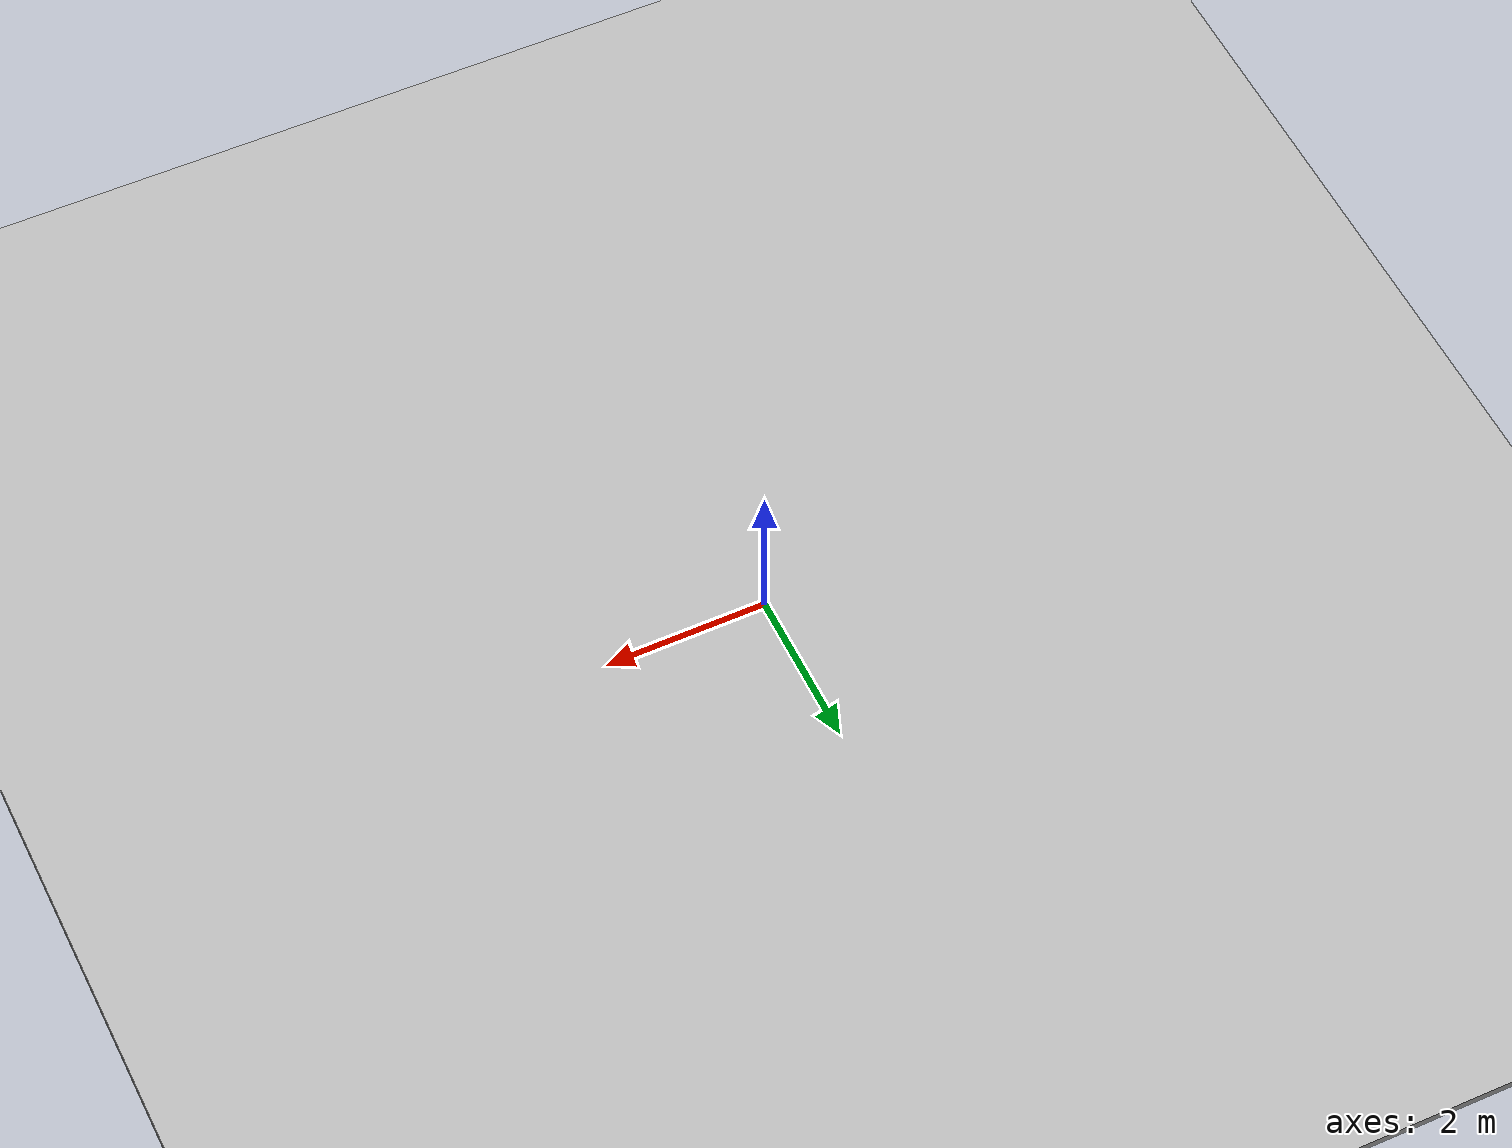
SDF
<sdf version="1.6">
 <world name="default">
  <model name="ground_plane">
   <static>1</static>
   <link name="link">
    <collision name="collision">
     <geometry><plane><normal>0 0 1</normal><size>100 100</size></plane></geometry>
     <surface><friction><ode><mu>100</mu><mu2>50</mu2></ode></friction></surface>
    </collision>
    <visual name="visual">
     <cast_shadows>0</cast_shadows>
     <geometry><plane><normal>0 0 1</normal><size>100 100</size></plane></geometry>
     <material>
      <script><uri>file://media/materials/scripts/gazebo.material</uri><name>Gazebo/Grey</name></script>
     </material>
    </visual>
   </link>
  </model>
  <light name="sun" type="directional">
   <pose>0 0 10 0 -0 0</pose>
   <diffuse>0.8 0.8 0.8 1</diffuse>
   <specular>0.1 0.1 0.1 1</specular>
   <attenuation>
    <range>1000</range>
    <constant>0.9</constant>
    <linear>0.01</linear>
    <quadratic>0.001</quadratic>
   </attenuation>
   <direction>-0.5 0.5 -1</direction>
  </light>
  <plugin name="SetupWorld" filename="libgazebo_plugins.so"/>
  <gravity>0 0 -9.8</gravity>
  <magnetic_field>6e-06 2.3e-05 -4.2e-05</magnetic_field>
  <atmosphere type="adiabatic"/>
  <physics name="default_physics" default="0" type="ode">
   <max_step_size>0.001</max_step_size>
   <real_time_factor>1</real_time_factor>
   <real_time_update_rate>1000</real_time_update_rate>
  </physics>
  <scene><ambient>0.4 0.4 0.4 1</ambient><background>0.7 0.7 0.7 1</background><shadows>1</shadows></scene>
  <spherical_coordinates>
   <surface_model>EARTH_WGS84</surface_model>
   <latitude_deg>0</latitude_deg>
   <longitude_deg>0</longitude_deg>
   <elevation>0</elevation>
   <heading_deg>0</heading_deg>
  </spherical_coordinates>
  <model name="at0">
   <static>0</static>
   <link name="link">
    <inertial>
     <mass>0.01</mass>
     <inertia><ixx>4e-05</ixx><ixy>0</ixy><ixz>0</ixz><iyy>4e-05</iyy><iyz>0</iyz><izz>4e-05</izz></inertia>
    </inertial>
    <visual name="visual">
     <geometry><box><size>0.05 0.05 0.05</size></box></geometry>
     <material>
      <script>
       <uri>model://at0/materials/scripts</uri>
       <uri>model://at0/materials/textures</uri>
       <name>at0/Diffuse</name>
      </script>
     </material>
    </visual>
    <collision name="collision">
     <geometry><box><size>0.05 0.05 0.05</size></box></geometry>
     <surface><friction><ode><mu>0.8</mu><mu2>0.7</mu2></ode></friction></surface>
    </collision>
   </link>
   <pose>-1.31449 4.47479 0.024993 2.9e-05 -2.9e-05 -1e-06</pose>
  </model>
  <model name="at1">
   <static>0</static>
   <link name="link">
    <inertial>
     <mass>0.01</mass>
     <inertia><ixx>4e-05</ixx><ixy>0</ixy><ixz>0</ixz><iyy>4e-05</iyy><iyz>0</iyz><izz>4e-05</izz></inertia>
    </inertial>
    <visual name="visual">
     <geometry><box><size>0.05 0.05 0.05</size></box></geometry>
     <material>
      <script>
       <uri>model://at0/materials/scripts</uri>
       <uri>model://at0/materials/textures</uri>
       <name>at0/Diffuse</name>
      </script>
     </material>
    </visual>
    <collision name="collision">
     <geometry><box><size>0.05 0.05 0.05</size></box></geometry>
     <surface><friction><ode><mu>0.8</mu><mu2>0.7</mu2></ode></friction></surface>
    </collision>
   </link>
   <pose>-1.21449 4.47479 0.024993 2.9e-05 -2.9e-05 -1e-06</pose>
  </model>
  <model name="at2">
   <static>0</static>
   <link name="link">
    <inertial>
     <mass>0.01</mass>
     <inertia><ixx>4e-05</ixx><ixy>0</ixy><ixz>0</ixz><iyy>4e-05</iyy><iyz>0</iyz><izz>4e-05</izz></inertia>
    </inertial>
    <visual name="visual">
     <geometry><box><size>0.05 0.05 0.05</size></box></geometry>
     <material>
      <script>
       <uri>model://at0/materials/scripts</uri>
       <uri>model://at0/materials/textures</uri>
       <name>at0/Diffuse</name>
      </script>
     </material>
    </visual>
    <collision name="collision">
     <geometry><box><size>0.05 0.05 0.05</size></box></geometry>
     <surface><friction><ode><mu>0.8</mu><mu2>0.7</mu2></ode></friction></surface>
    </collision>
   </link>
   <pose>-1.11449 4.47479 0.024993 2.9e-05 -2.9e-05 -1e-06</pose>
  </model>
  <model name="at3">
   <static>0</static>
   <link name="link">
    <inertial>
     <mass>0.01</mass>
     <inertia><ixx>4e-05</ixx><ixy>0</ixy><ixz>0</ixz><iyy>4e-05</iyy><iyz>0</iyz><izz>4e-05</izz></inertia>
    </inertial>
    <visual name="visual">
     <geometry><box><size>0.05 0.05 0.05</size></box></geometry>
     <material>
      <script>
       <uri>model://at0/materials/scripts</uri>
       <uri>model://at0/materials/textures</uri>
       <name>at0/Diffuse</name>
      </script>
     </material>
    </visual>
    <collision name="collision">
     <geometry><box><size>0.05 0.05 0.05</size></box></geometry>
     <surface><friction><ode><mu>0.8</mu><mu2>0.7</mu2></ode></friction></surface>
    </collision>
   </link>
   <pose>-1.01449 4.47479 0.024993 2.9e-05 -2.9e-05 -1e-06</pose>
  </model>
  <model name="at4">
   <static>0</static>
   <link name="link">
    <inertial>
     <mass>0.01</mass>
     <inertia><ixx>4e-05</ixx><ixy>0</ixy><ixz>0</ixz><iyy>4e-05</iyy><iyz>0</iyz><izz>4e-05</izz></inertia>
    </inertial>
    <visual name="visual">
     <geometry><box><size>0.05 0.05 0.05</size></box></geometry>
     <material>
      <script>
       <uri>model://at0/materials/scripts</uri>
       <uri>model://at0/materials/textures</uri>
       <name>at0/Diffuse</name>
      </script>
     </material>
    </visual>
    <collision name="collision">
     <geometry><box><size>0.05 0.05 0.05</size></box></geometry>
     <surface><friction><ode><mu>0.8</mu><mu2>0.7</mu2></ode></friction></surface>
    </collision>
   </link>
   <pose>-0.914491 4.47479 0.024993 2.9e-05 -2.9e-05 -1e-06</pose>
  </model>
  <model name="at5">
   <static>0</static>
   <link name="link">
    <inertial>
     <mass>0.01</mass>
     <inertia><ixx>4e-05</ixx><ixy>0</ixy><ixz>0</ixz><iyy>4e-05</iyy><iyz>0</iyz><izz>4e-05</izz></inertia>
    </inertial>
    <visual name="visual">
     <geometry><box><size>0.05 0.05 0.05</size></box></geometry>
     <material>
      <script>
       <uri>model://at0/materials/scripts</uri>
       <uri>model://at0/materials/textures</uri>
       <name>at0/Diffuse</name>
      </script>
     </material>
    </visual>
    <collision name="collision">
     <geometry><box><size>0.05 0.05 0.05</size></box></geometry>
     <surface><friction><ode><mu>0.8</mu><mu2>0.7</mu2></ode></friction></surface>
    </collision>
   </link>
   <pose>-0.814491 4.47479 0.024993 2.9e-05 -2.9e-05 -1e-06</pose>
  </model>
  <model name="at6">
   <static>0</static>
   <link name="link">
    <inertial>
     <mass>0.01</mass>
     <inertia><ixx>4e-05</ixx><ixy>0</ixy><ixz>0</ixz><iyy>4e-05</iyy><iyz>0</iyz><izz>4e-05</izz></inertia>
    </inertial>
    <visual name="visual">
     <geometry><box><size>0.05 0.05 0.05</size></box></geometry>
     <material>
      <script>
       <uri>model://at0/materials/scripts</uri>
       <uri>model://at0/materials/textures</uri>
       <name>at0/Diffuse</name>
      </script>
     </material>
    </visual>
    <collision name="collision">
     <geometry><box><size>0.05 0.05 0.05</size></box></geometry>
     <surface><friction><ode><mu>0.8</mu><mu2>0.7</mu2></ode></friction></surface>
    </collision>
   </link>
   <pose>-0.714491 4.47479 0.024993 2.9e-05 -2.9e-05 -1e-06</pose>
  </model>
  <model name="at7">
   <static>0</static>
   <link name="link">
    <inertial>
     <mass>0.01</mass>
     <inertia><ixx>4e-05</ixx><ixy>0</ixy><ixz>0</ixz><iyy>4e-05</iyy><iyz>0</iyz><izz>4e-05</izz></inertia>
    </inertial>
    <visual name="visual">
     <geometry><box><size>0.05 0.05 0.05</size></box></geometry>
     <material>
      <script>
       <uri>model://at0/materials/scripts</uri>
       <uri>model://at0/materials/textures</uri>
       <name>at0/Diffuse</name>
      </script>
     </material>
    </visual>
    <collision name="collision">
     <geometry><box><size>0.05 0.05 0.05</size></box></geometry>
     <surface><friction><ode><mu>0.8</mu><mu2>0.7</mu2></ode></friction></surface>
    </collision>
   </link>
   <pose>-0.614491 4.47479 0.024993 2.9e-05 -2.9e-05 -1e-06</pose>
  </model>
  <model name="at8">
   <static>0</static>
   <link name="link">
    <inertial>
     <mass>0.01</mass>
     <inertia><ixx>4e-05</ixx><ixy>0</ixy><ixz>0</ixz><iyy>4e-05</iyy><iyz>0</iyz><izz>4e-05</izz></inertia>
    </inertial>
    <visual name="visual">
     <geometry><box><size>0.05 0.05 0.05</size></box></geometry>
     <material>
      <script>
       <uri>model://at0/materials/scripts</uri>
       <uri>model://at0/materials/textures</uri>
       <name>at0/Diffuse</name>
      </script>
     </material>
    </visual>
    <collision name="collision">
     <geometry><box><size>0.05 0.05 0.05</size></box></geometry>
     <surface><friction><ode><mu>0.8</mu><mu2>0.7</mu2></ode></friction></surface>
    </collision>
   </link>
   <pose>-1.31449 4.57479 0.024993 2.9e-05 -2.9e-05 -1e-06</pose>
  </model>
  <model name="at9">
   <static>0</static>
   <link name="link">
    <inertial>
     <mass>0.01</mass>
     <inertia><ixx>4e-05</ixx><ixy>0</ixy><ixz>0</ixz><iyy>4e-05</iyy><iyz>0</iyz><izz>4e-05</izz></inertia>
    </inertial>
    <visual name="visual">
     <geometry><box><size>0.05 0.05 0.05</size></box></geometry>
     <material>
      <script>
       <uri>model://at0/materials/scripts</uri>
       <uri>model://at0/materials/textures</uri>
       <name>at0/Diffuse</name>
      </script>
     </material>
    </visual>
    <collision name="collision">
     <geometry><box><size>0.05 0.05 0.05</size></box></geometry>
     <surface><friction><ode><mu>0.8</mu><mu2>0.7</mu2></ode></friction></surface>
    </collision>
   </link>
   <pose>-1.21449 4.57479 0.024993 2.9e-05 -2.9e-05 -1e-06</pose>
  </model>
  <model name="at10">
   <static>0</static>
   <link name="link">
    <inertial>
     <mass>0.01</mass>
     <inertia><ixx>4e-05</ixx><ixy>0</ixy><ixz>0</ixz><iyy>4e-05</iyy><iyz>0</iyz><izz>4e-05</izz></inertia>
    </inertial>
    <visual name="visual">
     <geometry><box><size>0.05 0.05 0.05</size></box></geometry>
     <material>
      <script>
       <uri>model://at0/materials/scripts</uri>
       <uri>model://at0/materials/textures</uri>
       <name>at0/Diffuse</name>
      </script>
     </material>
    </visual>
    <collision name="collision">
     <geometry><box><size>0.05 0.05 0.05</size></box></geometry>
     <surface><friction><ode><mu>0.8</mu><mu2>0.7</mu2></ode></friction></surface>
    </collision>
   </link>
   <pose>-1.11449 4.57479 0.024993 2.9e-05 -2.9e-05 -1e-06</pose>
  </model>
  <model name="at11">
   <static>0</static>
   <link name="link">
    <inertial>
     <mass>0.01</mass>
     <inertia><ixx>4e-05</ixx><ixy>0</ixy><ixz>0</ixz><iyy>4e-05</iyy><iyz>0</iyz><izz>4e-05</izz></inertia>
    </inertial>
    <visual name="visual">
     <geometry><box><size>0.05 0.05 0.05</size></box></geometry>
     <material>
      <script>
       <uri>model://at0/materials/scripts</uri>
       <uri>model://at0/materials/textures</uri>
       <name>at0/Diffuse</name>
      </script>
     </material>
    </visual>
    <collision name="collision">
     <geometry><box><size>0.05 0.05 0.05</size></box></geometry>
     <surface><friction><ode><mu>0.8</mu><mu2>0.7</mu2></ode></friction></surface>
    </collision>
   </link>
   <pose>-1.01449 4.57479 0.024993 2.9e-05 -2.9e-05 -1e-06</pose>
  </model>
  <model name="at12">
   <static>0</static>
   <link name="link">
    <inertial>
     <mass>0.01</mass>
     <inertia><ixx>4e-05</ixx><ixy>0</ixy><ixz>0</ixz><iyy>4e-05</iyy><iyz>0</iyz><izz>4e-05</izz></inertia>
    </inertial>
    <visual name="visual">
     <geometry><box><size>0.05 0.05 0.05</size></box></geometry>
     <material>
      <script>
       <uri>model://at0/materials/scripts</uri>
       <uri>model://at0/materials/textures</uri>
       <name>at0/Diffuse</name>
      </script>
     </material>
    </visual>
    <collision name="collision">
     <geometry><box><size>0.05 0.05 0.05</size></box></geometry>
     <surface><friction><ode><mu>0.8</mu><mu2>0.7</mu2></ode></friction></surface>
    </collision>
   </link>
   <pose>-0.914491 4.57479 0.024993 2.9e-05 -2.9e-05 -1e-06</pose>
  </model>
  <model name="at13">
   <static>0</static>
   <link name="link">
    <inertial>
     <mass>0.01</mass>
     <inertia><ixx>4e-05</ixx><ixy>0</ixy><ixz>0</ixz><iyy>4e-05</iyy><iyz>0</iyz><izz>4e-05</izz></inertia>
    </inertial>
    <visual name="visual">
     <geometry><box><size>0.05 0.05 0.05</size></box></geometry>
     <material>
      <script>
       <uri>model://at0/materials/scripts</uri>
       <uri>model://at0/materials/textures</uri>
       <name>at0/Diffuse</name>
      </script>
     </material>
    </visual>
    <collision name="collision">
     <geometry><box><size>0.05 0.05 0.05</size></box></geometry>
     <surface><friction><ode><mu>0.8</mu><mu2>0.7</mu2></ode></friction></surface>
    </collision>
   </link>
   <pose>-0.814491 4.57479 0.024993 2.9e-05 -2.9e-05 -1e-06</pose>
  </model>
  <model name="at14">
   <static>0</static>
   <link name="link">
    <inertial>
     <mass>0.01</mass>
     <inertia><ixx>4e-05</ixx><ixy>0</ixy><ixz>0</ixz><iyy>4e-05</iyy><iyz>0</iyz><izz>4e-05</izz></inertia>
    </inertial>
    <visual name="visual">
     <geometry><box><size>0.05 0.05 0.05</size></box></geometry>
     <material>
      <script>
       <uri>model://at0/materials/scripts</uri>
       <uri>model://at0/materials/textures</uri>
       <name>at0/Diffuse</name>
      </script>
     </material>
    </visual>
    <collision name="collision">
     <geometry><box><size>0.05 0.05 0.05</size></box></geometry>
     <surface><friction><ode><mu>0.8</mu><mu2>0.7</mu2></ode></friction></surface>
    </collision>
   </link>
   <pose>-0.714491 4.57479 0.024993 2.9e-05 -2.9e-05 -1e-06</pose>
  </model>
  <model name="at15">
   <static>0</static>
   <link name="link">
    <inertial>
     <mass>0.01</mass>
     <inertia><ixx>4e-05</ixx><ixy>0</ixy><ixz>0</ixz><iyy>4e-05</iyy><iyz>0</iyz><izz>4e-05</izz></inertia>
    </inertial>
    <visual name="visual">
     <geometry><box><size>0.05 0.05 0.05</size></box></geometry>
     <material>
      <script>
       <uri>model://at0/materials/scripts</uri>
       <uri>model://at0/materials/textures</uri>
       <name>at0/Diffuse</name>
      </script>
     </material>
    </visual>
    <collision name="collision">
     <geometry><box><size>0.05 0.05 0.05</size></box></geometry>
     <surface><friction><ode><mu>0.8</mu><mu2>0.7</mu2></ode></friction></surface>
    </collision>
   </link>
   <pose>-0.614491 4.57479 0.024993 2.9e-05 -2.9e-05 -1e-06</pose>
  </model>
  <model name="at16">
   <static>0</static>
   <link name="link">
    <inertial>
     <mass>0.01</mass>
     <inertia><ixx>4e-05</ixx><ixy>0</ixy><ixz>0</ixz><iyy>4e-05</iyy><iyz>0</iyz><izz>4e-05</izz></inertia>
    </inertial>
    <visual name="visual">
     <geometry><box><size>0.05 0.05 0.05</size></box></geometry>
     <material>
      <script>
       <uri>model://at0/materials/scripts</uri>
       <uri>model://at0/materials/textures</uri>
       <name>at0/Diffuse</name>
      </script>
     </material>
    </visual>
    <collision name="collision">
     <geometry><box><size>0.05 0.05 0.05</size></box></geometry>
     <surface><friction><ode><mu>0.8</mu><mu2>0.7</mu2></ode></friction></surface>
    </collision>
   </link>
   <pose>-1.31449 4.67479 0.024993 2.9e-05 -2.9e-05 -1e-06</pose>
  </model>
  <model name="at17">
   <static>0</static>
   <link name="link">
    <inertial>
     <mass>0.01</mass>
     <inertia><ixx>4e-05</ixx><ixy>0</ixy><ixz>0</ixz><iyy>4e-05</iyy><iyz>0</iyz><izz>4e-05</izz></inertia>
    </inertial>
    <visual name="visual">
     <geometry><box><size>0.05 0.05 0.05</size></box></geometry>
     <material>
      <script>
       <uri>model://at0/materials/scripts</uri>
       <uri>model://at0/materials/textures</uri>
       <name>at0/Diffuse</name>
      </script>
     </material>
    </visual>
    <collision name="collision">
     <geometry><box><size>0.05 0.05 0.05</size></box></geometry>
     <surface><friction><ode><mu>0.8</mu><mu2>0.7</mu2></ode></friction></surface>
    </collision>
   </link>
   <pose>-1.21449 4.67479 0.024993 2.9e-05 -2.9e-05 -1e-06</pose>
  </model>
  <model name="at18">
   <static>0</static>
   <link name="link">
    <inertial>
     <mass>0.01</mass>
     <inertia><ixx>4e-05</ixx><ixy>0</ixy><ixz>0</ixz><iyy>4e-05</iyy><iyz>0</iyz><izz>4e-05</izz></inertia>
    </inertial>
    <visual name="visual">
     <geometry><box><size>0.05 0.05 0.05</size></box></geometry>
     <material>
      <script>
       <uri>model://at0/materials/scripts</uri>
       <uri>model://at0/materials/textures</uri>
       <name>at0/Diffuse</name>
      </script>
     </material>
    </visual>
    <collision name="collision">
     <geometry><box><size>0.05 0.05 0.05</size></box></geometry>
     <surface><friction><ode><mu>0.8</mu><mu2>0.7</mu2></ode></friction></surface>
    </collision>
   </link>
   <pose>-1.11449 4.67479 0.024993 2.9e-05 -2.9e-05 -1e-06</pose>
  </model>
  <model name="at19">
   <static>0</static>
   <link name="link">
    <inertial>
     <mass>0.01</mass>
     <inertia><ixx>4e-05</ixx><ixy>0</ixy><ixz>0</ixz><iyy>4e-05</iyy><iyz>0</iyz><izz>4e-05</izz></inertia>
    </inertial>
    <visual name="visual">
     <geometry><box><size>0.05 0.05 0.05</size></box></geometry>
     <material>
      <script>
       <uri>model://at0/materials/scripts</uri>
       <uri>model://at0/materials/textures</uri>
       <name>at0/Diffuse</name>
      </script>
     </material>
    </visual>
    <collision name="collision">
     <geometry><box><size>0.05 0.05 0.05</size></box></geometry>
     <surface><friction><ode><mu>0.8</mu><mu2>0.7</mu2></ode></friction></surface>
    </collision>
   </link>
   <pose>-1.01449 4.67479 0.024993 2.9e-05 -2.9e-05 -1e-06</pose>
  </model>
  <model name="at20">
   <static>0</static>
   <link name="link">
    <inertial>
     <mass>0.01</mass>
     <inertia><ixx>4e-05</ixx><ixy>0</ixy><ixz>0</ixz><iyy>4e-05</iyy><iyz>0</iyz><izz>4e-05</izz></inertia>
    </inertial>
    <visual name="visual">
     <geometry><box><size>0.05 0.05 0.05</size></box></geometry>
     <material>
      <script>
       <uri>model://at0/materials/scripts</uri>
       <uri>model://at0/materials/textures</uri>
       <name>at0/Diffuse</name>
      </script>
     </material>
    </visual>
    <collision name="collision">
     <geometry><box><size>0.05 0.05 0.05</size></box></geometry>
     <surface><friction><ode><mu>0.8</mu><mu2>0.7</mu2></ode></friction></surface>
    </collision>
   </link>
   <pose>-0.914491 4.67479 0.024993 2.9e-05 -2.9e-05 -1e-06</pose>
  </model>
  <model name="at21">
   <static>0</static>
   <link name="link">
    <inertial>
     <mass>0.01</mass>
     <inertia><ixx>4e-05</ixx><ixy>0</ixy><ixz>0</ixz><iyy>4e-05</iyy><iyz>0</iyz><izz>4e-05</izz></inertia>
    </inertial>
    <visual name="visual">
     <geometry><box><size>0.05 0.05 0.05</size></box></geometry>
     <material>
      <script>
       <uri>model://at0/materials/scripts</uri>
       <uri>model://at0/materials/textures</uri>
       <name>at0/Diffuse</name>
      </script>
     </material>
    </visual>
    <collision name="collision">
     <geometry><box><size>0.05 0.05 0.05</size></box></geometry>
     <surface><friction><ode><mu>0.8</mu><mu2>0.7</mu2></ode></friction></surface>
    </collision>
   </link>
   <pose>-0.814491 4.67479 0.024993 2.9e-05 -2.9e-05 -1e-06</pose>
  </model>
  <model name="at22">
   <static>0</static>
   <link name="link">
    <inertial>
     <mass>0.01</mass>
     <inertia><ixx>4e-05</ixx><ixy>0</ixy><ixz>0</ixz><iyy>4e-05</iyy><iyz>0</iyz><izz>4e-05</izz></inertia>
    </inertial>
    <visual name="visual">
     <geometry><box><size>0.05 0.05 0.05</size></box></geometry>
     <material>
      <script>
       <uri>model://at0/materials/scripts</uri>
       <uri>model://at0/materials/textures</uri>
       <name>at0/Diffuse</name>
      </script>
     </material>
    </visual>
    <collision name="collision">
     <geometry><box><size>0.05 0.05 0.05</size></box></geometry>
     <surface><friction><ode><mu>0.8</mu><mu2>0.7</mu2></ode></friction></surface>
    </collision>
   </link>
   <pose>-0.714491 4.67479 0.024993 2.9e-05 -2.9e-05 -1e-06</pose>
  </model>
  <model name="at23">
   <static>0</static>
   <link name="link">
    <inertial>
     <mass>0.01</mass>
     <inertia><ixx>4e-05</ixx><ixy>0</ixy><ixz>0</ixz><iyy>4e-05</iyy><iyz>0</iyz><izz>4e-05</izz></inertia>
    </inertial>
    <visual name="visual">
     <geometry><box><size>0.05 0.05 0.05</size></box></geometry>
     <material>
      <script>
       <uri>model://at0/materials/scripts</uri>
       <uri>model://at0/materials/textures</uri>
       <name>at0/Diffuse</name>
      </script>
     </material>
    </visual>
    <collision name="collision">
     <geometry><box><size>0.05 0.05 0.05</size></box></geometry>
     <surface><friction><ode><mu>0.8</mu><mu2>0.7</mu2></ode></friction></surface>
    </collision>
   </link>
   <pose>-0.614491 4.67479 0.024993 2.9e-05 -2.9e-05 -1e-06</pose>
  </model>
  <model name="at24">
   <static>0</static>
   <link name="link">
    <inertial>
     <mass>0.01</mass>
     <inertia><ixx>4e-05</ixx><ixy>0</ixy><ixz>0</ixz><iyy>4e-05</iyy><iyz>0</iyz><izz>4e-05</izz></inertia>
    </inertial>
    <visual name="visual">
     <geometry><box><size>0.05 0.05 0.05</size></box></geometry>
     <material>
      <script>
       <uri>model://at0/materials/scripts</uri>
       <uri>model://at0/materials/textures</uri>
       <name>at0/Diffuse</name>
      </script>
     </material>
    </visual>
    <collision name="collision">
     <geometry><box><size>0.05 0.05 0.05</size></box></geometry>
     <surface><friction><ode><mu>0.8</mu><mu2>0.7</mu2></ode></friction></surface>
    </collision>
   </link>
   <pose>-1.31449 4.77479 0.024993 2.9e-05 -2.9e-05 -1e-06</pose>
  </model>
  <model name="at25">
   <static>0</static>
   <link name="link">
    <inertial>
     <mass>0.01</mass>
     <inertia><ixx>4e-05</ixx><ixy>0</ixy><ixz>0</ixz><iyy>4e-05</iyy><iyz>0</iyz><izz>4e-05</izz></inertia>
    </inertial>
    <visual name="visual">
     <geometry><box><size>0.05 0.05 0.05</size></box></geometry>
     <material>
      <script>
       <uri>model://at0/materials/scripts</uri>
       <uri>model://at0/materials/textures</uri>
       <name>at0/Diffuse</name>
      </script>
     </material>
    </visual>
    <collision name="collision">
     <geometry><box><size>0.05 0.05 0.05</size></box></geometry>
     <surface><friction><ode><mu>0.8</mu><mu2>0.7</mu2></ode></friction></surface>
    </collision>
   </link>
   <pose>-1.21449 4.77479 0.024993 2.9e-05 -2.9e-05 -1e-06</pose>
  </model>
  <model name="at26">
   <static>0</static>
   <link name="link">
    <inertial>
     <mass>0.01</mass>
     <inertia><ixx>4e-05</ixx><ixy>0</ixy><ixz>0</ixz><iyy>4e-05</iyy><iyz>0</iyz><izz>4e-05</izz></inertia>
    </inertial>
    <visual name="visual">
     <geometry><box><size>0.05 0.05 0.05</size></box></geometry>
     <material>
      <script>
       <uri>model://at0/materials/scripts</uri>
       <uri>model://at0/materials/textures</uri>
       <name>at0/Diffuse</name>
      </script>
     </material>
    </visual>
    <collision name="collision">
     <geometry><box><size>0.05 0.05 0.05</size></box></geometry>
     <surface><friction><ode><mu>0.8</mu><mu2>0.7</mu2></ode></friction></surface>
    </collision>
   </link>
   <pose>-1.11449 4.77479 0.024993 2.9e-05 -2.9e-05 -1e-06</pose>
  </model>
  <model name="at27">
   <static>0</static>
   <link name="link">
    <inertial>
     <mass>0.01</mass>
     <inertia><ixx>4e-05</ixx><ixy>0</ixy><ixz>0</ixz><iyy>4e-05</iyy><iyz>0</iyz><izz>4e-05</izz></inertia>
    </inertial>
    <visual name="visual">
     <geometry><box><size>0.05 0.05 0.05</size></box></geometry>
     <material>
      <script>
       <uri>model://at0/materials/scripts</uri>
       <uri>model://at0/materials/textures</uri>
       <name>at0/Diffuse</name>
      </script>
     </material>
    </visual>
    <collision name="collision">
     <geometry><box><size>0.05 0.05 0.05</size></box></geometry>
     <surface><friction><ode><mu>0.8</mu><mu2>0.7</mu2></ode></friction></surface>
    </collision>
   </link>
   <pose>-1.01449 4.77479 0.024993 2.9e-05 -2.9e-05 -1e-06</pose>
  </model>
  <model name="at28">
   <static>0</static>
   <link name="link">
    <inertial>
     <mass>0.01</mass>
     <inertia><ixx>4e-05</ixx><ixy>0</ixy><ixz>0</ixz><iyy>4e-05</iyy><iyz>0</iyz><izz>4e-05</izz></inertia>
    </inertial>
    <visual name="visual">
     <geometry><box><size>0.05 0.05 0.05</size></box></geometry>
     <material>
      <script>
       <uri>model://at0/materials/scripts</uri>
       <uri>model://at0/materials/textures</uri>
       <name>at0/Diffuse</name>
      </script>
     </material>
    </visual>
    <collision name="collision">
     <geometry><box><size>0.05 0.05 0.05</size></box></geometry>
     <surface><friction><ode><mu>0.8</mu><mu2>0.7</mu2></ode></friction></surface>
    </collision>
   </link>
   <pose>-0.914491 4.77479 0.024993 2.9e-05 -2.9e-05 -1e-06</pose>
  </model>
  <model name="at29">
   <static>0</static>
   <link name="link">
    <inertial>
     <mass>0.01</mass>
     <inertia><ixx>4e-05</ixx><ixy>0</ixy><ixz>0</ixz><iyy>4e-05</iyy><iyz>0</iyz><izz>4e-05</izz></inertia>
    </inertial>
    <visual name="visual">
     <geometry><box><size>0.05 0.05 0.05</size></box></geometry>
     <material>
      <script>
       <uri>model://at0/materials/scripts</uri>
       <uri>model://at0/materials/textures</uri>
       <name>at0/Diffuse</name>
      </script>
     </material>
    </visual>
    <collision name="collision">
     <geometry><box><size>0.05 0.05 0.05</size></box></geometry>
     <surface><friction><ode><mu>0.8</mu><mu2>0.7</mu2></ode></friction></surface>
    </collision>
   </link>
   <pose>-0.814491 4.77479 0.024993 2.9e-05 -2.9e-05 -1e-06</pose>
  </model>
  <model name="at30">
   <static>0</static>
   <link name="link">
    <inertial>
     <mass>0.01</mass>
     <inertia><ixx>4e-05</ixx><ixy>0</ixy><ixz>0</ixz><iyy>4e-05</iyy><iyz>0</iyz><izz>4e-05</izz></inertia>
    </inertial>
    <visual name="visual">
     <geometry><box><size>0.05 0.05 0.05</size></box></geometry>
     <material>
      <script>
       <uri>model://at0/materials/scripts</uri>
       <uri>model://at0/materials/textures</uri>
       <name>at0/Diffuse</name>
      </script>
     </material>
    </visual>
    <collision name="collision">
     <geometry><box><size>0.05 0.05 0.05</size></box></geometry>
     <surface><friction><ode><mu>0.8</mu><mu2>0.7</mu2></ode></friction></surface>
    </collision>
   </link>
   <pose>-0.714491 4.77479 0.024993 2.9e-05 -2.9e-05 -1e-06</pose>
  </model>
  <model name="at31">
   <static>0</static>
   <link name="link">
    <inertial>
     <mass>0.01</mass>
     <inertia><ixx>4e-05</ixx><ixy>0</ixy><ixz>0</ixz><iyy>4e-05</iyy><iyz>0</iyz><izz>4e-05</izz></inertia>
    </inertial>
    <visual name="visual">
     <geometry><box><size>0.05 0.05 0.05</size></box></geometry>
     <material>
      <script>
       <uri>model://at0/materials/scripts</uri>
       <uri>model://at0/materials/textures</uri>
       <name>at0/Diffuse</name>
      </script>
     </material>
    </visual>
    <collision name="collision">
     <geometry><box><size>0.05 0.05 0.05</size></box></geometry>
     <surface><friction><ode><mu>0.8</mu><mu2>0.7</mu2></ode></friction></surface>
    </collision>
   </link>
   <pose>-0.614491 4.77479 0.024993 2.9e-05 -2.9e-05 -1e-06</pose>
  </model>
  <model name="at32">
   <static>0</static>
   <link name="link">
    <inertial>
     <mass>0.01</mass>
     <inertia><ixx>4e-05</ixx><ixy>0</ixy><ixz>0</ixz><iyy>4e-05</iyy><iyz>0</iyz><izz>4e-05</izz></inertia>
    </inertial>
    <visual name="visual">
     <geometry><box><size>0.05 0.05 0.05</size></box></geometry>
     <material>
      <script>
       <uri>model://at0/materials/scripts</uri>
       <uri>model://at0/materials/textures</uri>
       <name>at0/Diffuse</name>
      </script>
     </material>
    </visual>
    <collision name="collision">
     <geometry><box><size>0.05 0.05 0.05</size></box></geometry>
     <surface><friction><ode><mu>0.8</mu><mu2>0.7</mu2></ode></friction></surface>
    </collision>
   </link>
   <pose>4.71616 1.51634 0.024993 2.9e-05 -2.9e-05 -1e-06</pose>
  </model>
  <model name="at33">
   <static>0</static>
   <link name="link">
    <inertial>
     <mass>0.01</mass>
     <inertia><ixx>4e-05</ixx><ixy>0</ixy><ixz>0</ixz><iyy>4e-05</iyy><iyz>0</iyz><izz>4e-05</izz></inertia>
    </inertial>
    <visual name="visual">
     <geometry><box><size>0.05 0.05 0.05</size></box></geometry>
     <material>
      <script>
       <uri>model://at0/materials/scripts</uri>
       <uri>model://at0/materials/textures</uri>
       <name>at0/Diffuse</name>
      </script>
     </material>
    </visual>
    <collision name="collision">
     <geometry><box><size>0.05 0.05 0.05</size></box></geometry>
     <surface><friction><ode><mu>0.8</mu><mu2>0.7</mu2></ode></friction></surface>
    </collision>
   </link>
   <pose>4.81616 1.51634 0.024993 2.9e-05 -2.9e-05 -1e-06</pose>
  </model>
  <model name="at34">
   <static>0</static>
   <link name="link">
    <inertial>
     <mass>0.01</mass>
     <inertia><ixx>4e-05</ixx><ixy>0</ixy><ixz>0</ixz><iyy>4e-05</iyy><iyz>0</iyz><izz>4e-05</izz></inertia>
    </inertial>
    <visual name="visual">
     <geometry><box><size>0.05 0.05 0.05</size></box></geometry>
     <material>
      <script>
       <uri>model://at0/materials/scripts</uri>
       <uri>model://at0/materials/textures</uri>
       <name>at0/Diffuse</name>
      </script>
     </material>
    </visual>
    <collision name="collision">
     <geometry><box><size>0.05 0.05 0.05</size></box></geometry>
     <surface><friction><ode><mu>0.8</mu><mu2>0.7</mu2></ode></friction></surface>
    </collision>
   </link>
   <pose>4.91616 1.51634 0.024993 2.9e-05 -2.9e-05 -1e-06</pose>
  </model>
  <model name="at35">
   <static>0</static>
   <link name="link">
    <inertial>
     <mass>0.01</mass>
     <inertia><ixx>4e-05</ixx><ixy>0</ixy><ixz>0</ixz><iyy>4e-05</iyy><iyz>0</iyz><izz>4e-05</izz></inertia>
    </inertial>
    <visual name="visual">
     <geometry><box><size>0.05 0.05 0.05</size></box></geometry>
     <material>
      <script>
       <uri>model://at0/materials/scripts</uri>
       <uri>model://at0/materials/textures</uri>
       <name>at0/Diffuse</name>
      </script>
     </material>
    </visual>
    <collision name="collision">
     <geometry><box><size>0.05 0.05 0.05</size></box></geometry>
     <surface><friction><ode><mu>0.8</mu><mu2>0.7</mu2></ode></friction></surface>
    </collision>
   </link>
   <pose>5.01616 1.51634 0.024993 2.9e-05 -2.9e-05 -1e-06</pose>
  </model>
  <model name="at36">
   <static>0</static>
   <link name="link">
    <inertial>
     <mass>0.01</mass>
     <inertia><ixx>4e-05</ixx><ixy>0</ixy><ixz>0</ixz><iyy>4e-05</iyy><iyz>0</iyz><izz>4e-05</izz></inertia>
    </inertial>
    <visual name="visual">
     <geometry><box><size>0.05 0.05 0.05</size></box></geometry>
     <material>
      <script>
       <uri>model://at0/materials/scripts</uri>
       <uri>model://at0/materials/textures</uri>
       <name>at0/Diffuse</name>
      </script>
     </material>
    </visual>
    <collision name="collision">
     <geometry><box><size>0.05 0.05 0.05</size></box></geometry>
     <surface><friction><ode><mu>0.8</mu><mu2>0.7</mu2></ode></friction></surface>
    </collision>
   </link>
   <pose>4.71616 1.61634 0.024993 2.9e-05 -2.9e-05 -1e-06</pose>
  </model>
  <model name="at37">
   <static>0</static>
   <link name="link">
    <inertial>
     <mass>0.01</mass>
     <inertia><ixx>4e-05</ixx><ixy>0</ixy><ixz>0</ixz><iyy>4e-05</iyy><iyz>0</iyz><izz>4e-05</izz></inertia>
    </inertial>
    <visual name="visual">
     <geometry><box><size>0.05 0.05 0.05</size></box></geometry>
     <material>
      <script>
       <uri>model://at0/materials/scripts</uri>
       <uri>model://at0/materials/textures</uri>
       <name>at0/Diffuse</name>
      </script>
     </material>
    </visual>
    <collision name="collision">
     <geometry><box><size>0.05 0.05 0.05</size></box></geometry>
     <surface><friction><ode><mu>0.8</mu><mu2>0.7</mu2></ode></friction></surface>
    </collision>
   </link>
   <pose>4.81616 1.61634 0.024993 2.9e-05 -2.9e-05 -1e-06</pose>
  </model>
  <model name="at38">
   <static>0</static>
   <link name="link">
    <inertial>
     <mass>0.01</mass>
     <inertia><ixx>4e-05</ixx><ixy>0</ixy><ixz>0</ixz><iyy>4e-05</iyy><iyz>0</iyz><izz>4e-05</izz></inertia>
    </inertial>
    <visual name="visual">
     <geometry><box><size>0.05 0.05 0.05</size></box></geometry>
     <material>
      <script>
       <uri>model://at0/materials/scripts</uri>
       <uri>model://at0/materials/textures</uri>
       <name>at0/Diffuse</name>
      </script>
     </material>
    </visual>
    <collision name="collision">
     <geometry><box><size>0.05 0.05 0.05</size></box></geometry>
     <surface><friction><ode><mu>0.8</mu><mu2>0.7</mu2></ode></friction></surface>
    </collision>
   </link>
   <pose>4.91616 1.61634 0.024993 2.9e-05 -2.9e-05 -1e-06</pose>
  </model>
  <model name="at39">
   <static>0</static>
   <link name="link">
    <inertial>
     <mass>0.01</mass>
     <inertia><ixx>4e-05</ixx><ixy>0</ixy><ixz>0</ixz><iyy>4e-05</iyy><iyz>0</iyz><izz>4e-05</izz></inertia>
    </inertial>
    <visual name="visual">
     <geometry><box><size>0.05 0.05 0.05</size></box></geometry>
     <material>
      <script>
       <uri>model://at0/materials/scripts</uri>
       <uri>model://at0/materials/textures</uri>
       <name>at0/Diffuse</name>
      </script>
     </material>
    </visual>
    <collision name="collision">
     <geometry><box><size>0.05 0.05 0.05</size></box></geometry>
     <surface><friction><ode><mu>0.8</mu><mu2>0.7</mu2></ode></friction></surface>
    </collision>
   </link>
   <pose>5.01616 1.61634 0.024993 2.9e-05 -2.9e-05 -1e-06</pose>
  </model>
  <model name="at40">
   <static>0</static>
   <link name="link">
    <inertial>
     <mass>0.01</mass>
     <inertia><ixx>4e-05</ixx><ixy>0</ixy><ixz>0</ixz><iyy>4e-05</iyy><iyz>0</iyz><izz>4e-05</izz></inertia>
    </inertial>
    <visual name="visual">
     <geometry><box><size>0.05 0.05 0.05</size></box></geometry>
     <material>
      <script>
       <uri>model://at0/materials/scripts</uri>
       <uri>model://at0/materials/textures</uri>
       <name>at0/Diffuse</name>
      </script>
     </material>
    </visual>
    <collision name="collision">
     <geometry><box><size>0.05 0.05 0.05</size></box></geometry>
     <surface><friction><ode><mu>0.8</mu><mu2>0.7</mu2></ode></friction></surface>
    </collision>
   </link>
   <pose>4.71616 1.71634 0.024993 2.9e-05 -2.9e-05 -1e-06</pose>
  </model>
  <model name="at41">
   <static>0</static>
   <link name="link">
    <inertial>
     <mass>0.01</mass>
     <inertia><ixx>4e-05</ixx><ixy>0</ixy><ixz>0</ixz><iyy>4e-05</iyy><iyz>0</iyz><izz>4e-05</izz></inertia>
    </inertial>
    <visual name="visual">
     <geometry><box><size>0.05 0.05 0.05</size></box></geometry>
     <material>
      <script>
       <uri>model://at0/materials/scripts</uri>
       <uri>model://at0/materials/textures</uri>
       <name>at0/Diffuse</name>
      </script>
     </material>
    </visual>
    <collision name="collision">
     <geometry><box><size>0.05 0.05 0.05</size></box></geometry>
     <surface><friction><ode><mu>0.8</mu><mu2>0.7</mu2></ode></friction></surface>
    </collision>
   </link>
   <pose>4.81616 1.71634 0.024993 2.9e-05 -2.9e-05 -1e-06</pose>
  </model>
  <model name="at42">
   <static>0</static>
   <link name="link">
    <inertial>
     <mass>0.01</mass>
     <inertia><ixx>4e-05</ixx><ixy>0</ixy><ixz>0</ixz><iyy>4e-05</iyy><iyz>0</iyz><izz>4e-05</izz></inertia>
    </inertial>
    <visual name="visual">
     <geometry><box><size>0.05 0.05 0.05</size></box></geometry>
     <material>
      <script>
       <uri>model://at0/materials/scripts</uri>
       <uri>model://at0/materials/textures</uri>
       <name>at0/Diffuse</name>
      </script>
     </material>
    </visual>
    <collision name="collision">
     <geometry><box><size>0.05 0.05 0.05</size></box></geometry>
     <surface><friction><ode><mu>0.8</mu><mu2>0.7</mu2></ode></friction></surface>
    </collision>
   </link>
   <pose>4.91616 1.71634 0.024993 2.9e-05 -2.9e-05 -1e-06</pose>
  </model>
  <model name="at43">
   <static>0</static>
   <link name="link">
    <inertial>
     <mass>0.01</mass>
     <inertia><ixx>4e-05</ixx><ixy>0</ixy><ixz>0</ixz><iyy>4e-05</iyy><iyz>0</iyz><izz>4e-05</izz></inertia>
    </inertial>
    <visual name="visual">
     <geometry><box><size>0.05 0.05 0.05</size></box></geometry>
     <material>
      <script>
       <uri>model://at0/materials/scripts</uri>
       <uri>model://at0/materials/textures</uri>
       <name>at0/Diffuse</name>
      </script>
     </material>
    </visual>
    <collision name="collision">
     <geometry><box><size>0.05 0.05 0.05</size></box></geometry>
     <surface><friction><ode><mu>0.8</mu><mu2>0.7</mu2></ode></friction></surface>
    </collision>
   </link>
   <pose>5.01616 1.71634 0.024993 2.9e-05 -2.9e-05 -1e-06</pose>
  </model>
  <model name="at44">
   <static>0</static>
   <link name="link">
    <inertial>
     <mass>0.01</mass>
     <inertia><ixx>4e-05</ixx><ixy>0</ixy><ixz>0</ixz><iyy>4e-05</iyy><iyz>0</iyz><izz>4e-05</izz></inertia>
    </inertial>
    <visual name="visual">
     <geometry><box><size>0.05 0.05 0.05</size></box></geometry>
     <material>
      <script>
       <uri>model://at0/materials/scripts</uri>
       <uri>model://at0/materials/textures</uri>
       <name>at0/Diffuse</name>
      </script>
     </material>
    </visual>
    <collision name="collision">
     <geometry><box><size>0.05 0.05 0.05</size></box></geometry>
     <surface><friction><ode><mu>0.8</mu><mu2>0.7</mu2></ode></friction></surface>
    </collision>
   </link>
   <pose>4.71616 1.81634 0.024993 2.9e-05 -2.9e-05 -1e-06</pose>
  </model>
  <model name="at45">
   <static>0</static>
   <link name="link">
    <inertial>
     <mass>0.01</mass>
     <inertia><ixx>4e-05</ixx><ixy>0</ixy><ixz>0</ixz><iyy>4e-05</iyy><iyz>0</iyz><izz>4e-05</izz></inertia>
    </inertial>
    <visual name="visual">
     <geometry><box><size>0.05 0.05 0.05</size></box></geometry>
     <material>
      <script>
       <uri>model://at0/materials/scripts</uri>
       <uri>model://at0/materials/textures</uri>
       <name>at0/Diffuse</name>
      </script>
     </material>
    </visual>
    <collision name="collision">
     <geometry><box><size>0.05 0.05 0.05</size></box></geometry>
     <surface><friction><ode><mu>0.8</mu><mu2>0.7</mu2></ode></friction></surface>
    </collision>
   </link>
   <pose>4.81616 1.81634 0.024993 2.9e-05 -2.9e-05 -1e-06</pose>
  </model>
  <model name="at46">
   <static>0</static>
   <link name="link">
    <inertial>
     <mass>0.01</mass>
     <inertia><ixx>4e-05</ixx><ixy>0</ixy><ixz>0</ixz><iyy>4e-05</iyy><iyz>0</iyz><izz>4e-05</izz></inertia>
    </inertial>
    <visual name="visual">
     <geometry><box><size>0.05 0.05 0.05</size></box></geometry>
     <material>
      <script>
       <uri>model://at0/materials/scripts</uri>
       <uri>model://at0/materials/textures</uri>
       <name>at0/Diffuse</name>
      </script>
     </material>
    </visual>
    <collision name="collision">
     <geometry><box><size>0.05 0.05 0.05</size></box></geometry>
     <surface><friction><ode><mu>0.8</mu><mu2>0.7</mu2></ode></friction></surface>
    </collision>
   </link>
   <pose>4.91616 1.81634 0.024993 2.9e-05 -2.9e-05 -1e-06</pose>
  </model>
  <model name="at47">
   <static>0</static>
   <link name="link">
    <inertial>
     <mass>0.01</mass>
     <inertia><ixx>4e-05</ixx><ixy>0</ixy><ixz>0</ixz><iyy>4e-05</iyy><iyz>0</iyz><izz>4e-05</izz></inertia>
    </inertial>
    <visual name="visual">
     <geometry><box><size>0.05 0.05 0.05</size></box></geometry>
     <material>
      <script>
       <uri>model://at0/materials/scripts</uri>
       <uri>model://at0/materials/textures</uri>
       <name>at0/Diffuse</name>
      </script>
     </material>
    </visual>
    <collision name="collision">
     <geometry><box><size>0.05 0.05 0.05</size></box></geometry>
     <surface><friction><ode><mu>0.8</mu><mu2>0.7</mu2></ode></friction></surface>
    </collision>
   </link>
   <pose>5.01616 1.81634 0.024993 2.9e-05 -2.9e-05 -1e-06</pose>
  </model>
  <model name="at48">
   <static>0</static>
   <link name="link">
    <inertial>
     <mass>0.01</mass>
     <inertia><ixx>4e-05</ixx><ixy>0</ixy><ixz>0</ixz><iyy>4e-05</iyy><iyz>0</iyz><izz>4e-05</izz></inertia>
    </inertial>
    <visual name="visual">
     <geometry><box><size>0.05 0.05 0.05</size></box></geometry>
     <material>
      <script>
       <uri>model://at0/materials/scripts</uri>
       <uri>model://at0/materials/textures</uri>
       <name>at0/Diffuse</name>
      </script>
     </material>
    </visual>
    <collision name="collision">
     <geometry><box><size>0.05 0.05 0.05</size></box></geometry>
     <surface><friction><ode><mu>0.8</mu><mu2>0.7</mu2></ode></friction></surface>
    </collision>
   </link>
   <pose>-5.78237 -4.47573 0.024993 2.9e-05 -2.9e-05 -1e-06</pose>
  </model>
  <model name="at49">
   <static>0</static>
   <link name="link">
    <inertial>
     <mass>0.01</mass>
     <inertia><ixx>4e-05</ixx><ixy>0</ixy><ixz>0</ixz><iyy>4e-05</iyy><iyz>0</iyz><izz>4e-05</izz></inertia>
    </inertial>
    <visual name="visual">
     <geometry><box><size>0.05 0.05 0.05</size></box></geometry>
     <material>
      <script>
       <uri>model://at0/materials/scripts</uri>
       <uri>model://at0/materials/textures</uri>
       <name>at0/Diffuse</name>
      </script>
     </material>
    </visual>
    <collision name="collision">
     <geometry><box><size>0.05 0.05 0.05</size></box></geometry>
     <surface><friction><ode><mu>0.8</mu><mu2>0.7</mu2></ode></friction></surface>
    </collision>
   </link>
   <pose>-5.68237 -4.47573 0.024993 2.9e-05 -2.9e-05 -1e-06</pose>
  </model>
  <model name="at50">
   <static>0</static>
   <link name="link">
    <inertial>
     <mass>0.01</mass>
     <inertia><ixx>4e-05</ixx><ixy>0</ixy><ixz>0</ixz><iyy>4e-05</iyy><iyz>0</iyz><izz>4e-05</izz></inertia>
    </inertial>
    <visual name="visual">
     <geometry><box><size>0.05 0.05 0.05</size></box></geometry>
     <material>
      <script>
       <uri>model://at0/materials/scripts</uri>
       <uri>model://at0/materials/textures</uri>
       <name>at0/Diffuse</name>
      </script>
     </material>
    </visual>
    <collision name="collision">
     <geometry><box><size>0.05 0.05 0.05</size></box></geometry>
     <surface><friction><ode><mu>0.8</mu><mu2>0.7</mu2></ode></friction></surface>
    </collision>
   </link>
   <pose>-5.58237 -4.47573 0.024993 2.9e-05 -2.9e-05 -1e-06</pose>
  </model>
  <model name="at51">
   <static>0</static>
   <link name="link">
    <inertial>
     <mass>0.01</mass>
     <inertia><ixx>4e-05</ixx><ixy>0</ixy><ixz>0</ixz><iyy>4e-05</iyy><iyz>0</iyz><izz>4e-05</izz></inertia>
    </inertial>
    <visual name="visual">
     <geometry><box><size>0.05 0.05 0.05</size></box></geometry>
     <material>
      <script>
       <uri>model://at0/materials/scripts</uri>
       <uri>model://at0/materials/textures</uri>
       <name>at0/Diffuse</name>
      </script>
     </material>
    </visual>
    <collision name="collision">
     <geometry><box><size>0.05 0.05 0.05</size></box></geometry>
     <surface><friction><ode><mu>0.8</mu><mu2>0.7</mu2></ode></friction></surface>
    </collision>
   </link>
   <pose>-5.48237 -4.47573 0.024993 2.9e-05 -2.9e-05 -1e-06</pose>
  </model>
  <model name="at52">
   <static>0</static>
   <link name="link">
    <inertial>
     <mass>0.01</mass>
     <inertia><ixx>4e-05</ixx><ixy>0</ixy><ixz>0</ixz><iyy>4e-05</iyy><iyz>0</iyz><izz>4e-05</izz></inertia>
    </inertial>
    <visual name="visual">
     <geometry><box><size>0.05 0.05 0.05</size></box></geometry>
     <material>
      <script>
       <uri>model://at0/materials/scripts</uri>
       <uri>model://at0/materials/textures</uri>
       <name>at0/Diffuse</name>
      </script>
     </material>
    </visual>
    <collision name="collision">
     <geometry><box><size>0.05 0.05 0.05</size></box></geometry>
     <surface><friction><ode><mu>0.8</mu><mu2>0.7</mu2></ode></friction></surface>
    </collision>
   </link>
   <pose>-5.78237 -4.37573 0.024993 2.9e-05 -2.9e-05 -1e-06</pose>
  </model>
  <model name="at53">
   <static>0</static>
   <link name="link">
    <inertial>
     <mass>0.01</mass>
     <inertia><ixx>4e-05</ixx><ixy>0</ixy><ixz>0</ixz><iyy>4e-05</iyy><iyz>0</iyz><izz>4e-05</izz></inertia>
    </inertial>
    <visual name="visual">
     <geometry><box><size>0.05 0.05 0.05</size></box></geometry>
     <material>
      <script>
       <uri>model://at0/materials/scripts</uri>
       <uri>model://at0/materials/textures</uri>
       <name>at0/Diffuse</name>
      </script>
     </material>
    </visual>
    <collision name="collision">
     <geometry><box><size>0.05 0.05 0.05</size></box></geometry>
     <surface><friction><ode><mu>0.8</mu><mu2>0.7</mu2></ode></friction></surface>
    </collision>
   </link>
   <pose>-5.68237 -4.37573 0.024993 2.9e-05 -2.9e-05 -1e-06</pose>
  </model>
  <model name="at54">
   <static>0</static>
   <link name="link">
    <inertial>
     <mass>0.01</mass>
     <inertia><ixx>4e-05</ixx><ixy>0</ixy><ixz>0</ixz><iyy>4e-05</iyy><iyz>0</iyz><izz>4e-05</izz></inertia>
    </inertial>
    <visual name="visual">
     <geometry><box><size>0.05 0.05 0.05</size></box></geometry>
     <material>
      <script>
       <uri>model://at0/materials/scripts</uri>
       <uri>model://at0/materials/textures</uri>
       <name>at0/Diffuse</name>
      </script>
     </material>
    </visual>
    <collision name="collision">
     <geometry><box><size>0.05 0.05 0.05</size></box></geometry>
     <surface><friction><ode><mu>0.8</mu><mu2>0.7</mu2></ode></friction></surface>
    </collision>
   </link>
   <pose>-5.58237 -4.37573 0.024993 2.9e-05 -2.9e-05 -1e-06</pose>
  </model>
  <model name="at55">
   <static>0</static>
   <link name="link">
    <inertial>
     <mass>0.01</mass>
     <inertia><ixx>4e-05</ixx><ixy>0</ixy><ixz>0</ixz><iyy>4e-05</iyy><iyz>0</iyz><izz>4e-05</izz></inertia>
    </inertial>
    <visual name="visual">
     <geometry><box><size>0.05 0.05 0.05</size></box></geometry>
     <material>
      <script>
       <uri>model://at0/materials/scripts</uri>
       <uri>model://at0/materials/textures</uri>
       <name>at0/Diffuse</name>
      </script>
     </material>
    </visual>
    <collision name="collision">
     <geometry><box><size>0.05 0.05 0.05</size></box></geometry>
     <surface><friction><ode><mu>0.8</mu><mu2>0.7</mu2></ode></friction></surface>
    </collision>
   </link>
   <pose>-5.48237 -4.37573 0.024993 2.9e-05 -2.9e-05 -1e-06</pose>
  </model>
  <model name="at56">
   <static>0</static>
   <link name="link">
    <inertial>
     <mass>0.01</mass>
     <inertia><ixx>4e-05</ixx><ixy>0</ixy><ixz>0</ixz><iyy>4e-05</iyy><iyz>0</iyz><izz>4e-05</izz></inertia>
    </inertial>
    <visual name="visual">
     <geometry><box><size>0.05 0.05 0.05</size></box></geometry>
     <material>
      <script>
       <uri>model://at0/materials/scripts</uri>
       <uri>model://at0/materials/textures</uri>
       <name>at0/Diffuse</name>
      </script>
     </material>
    </visual>
    <collision name="collision">
     <geometry><box><size>0.05 0.05 0.05</size></box></geometry>
     <surface><friction><ode><mu>0.8</mu><mu2>0.7</mu2></ode></friction></surface>
    </collision>
   </link>
   <pose>-5.78237 -4.27573 0.024993 2.9e-05 -2.9e-05 -1e-06</pose>
  </model>
  <model name="at57">
   <static>0</static>
   <link name="link">
    <inertial>
     <mass>0.01</mass>
     <inertia><ixx>4e-05</ixx><ixy>0</ixy><ixz>0</ixz><iyy>4e-05</iyy><iyz>0</iyz><izz>4e-05</izz></inertia>
    </inertial>
    <visual name="visual">
     <geometry><box><size>0.05 0.05 0.05</size></box></geometry>
     <material>
      <script>
       <uri>model://at0/materials/scripts</uri>
       <uri>model://at0/materials/textures</uri>
       <name>at0/Diffuse</name>
      </script>
     </material>
    </visual>
    <collision name="collision">
     <geometry><box><size>0.05 0.05 0.05</size></box></geometry>
     <surface><friction><ode><mu>0.8</mu><mu2>0.7</mu2></ode></friction></surface>
    </collision>
   </link>
   <pose>-5.68237 -4.27573 0.024993 2.9e-05 -2.9e-05 -1e-06</pose>
  </model>
  <model name="at58">
   <static>0</static>
   <link name="link">
    <inertial>
     <mass>0.01</mass>
     <inertia><ixx>4e-05</ixx><ixy>0</ixy><ixz>0</ixz><iyy>4e-05</iyy><iyz>0</iyz><izz>4e-05</izz></inertia>
    </inertial>
    <visual name="visual">
     <geometry><box><size>0.05 0.05 0.05</size></box></geometry>
     <material>
      <script>
       <uri>model://at0/materials/scripts</uri>
       <uri>model://at0/materials/textures</uri>
       <name>at0/Diffuse</name>
      </script>
     </material>
    </visual>
    <collision name="collision">
     <geometry><box><size>0.05 0.05 0.05</size></box></geometry>
     <surface><friction><ode><mu>0.8</mu><mu2>0.7</mu2></ode></friction></surface>
    </collision>
   </link>
   <pose>-5.58237 -4.27573 0.024993 2.9e-05 -2.9e-05 -1e-06</pose>
  </model>
  <model name="at59">
   <static>0</static>
   <link name="link">
    <inertial>
     <mass>0.01</mass>
     <inertia><ixx>4e-05</ixx><ixy>0</ixy><ixz>0</ixz><iyy>4e-05</iyy><iyz>0</iyz><izz>4e-05</izz></inertia>
    </inertial>
    <visual name="visual">
     <geometry><box><size>0.05 0.05 0.05</size></box></geometry>
     <material>
      <script>
       <uri>model://at0/materials/scripts</uri>
       <uri>model://at0/materials/textures</uri>
       <name>at0/Diffuse</name>
      </script>
     </material>
    </visual>
    <collision name="collision">
     <geometry><box><size>0.05 0.05 0.05</size></box></geometry>
     <surface><friction><ode><mu>0.8</mu><mu2>0.7</mu2></ode></friction></surface>
    </collision>
   </link>
   <pose>-5.48237 -4.27573 0.024993 2.9e-05 -2.9e-05 -1e-06</pose>
  </model>
  <model name="at60">
   <static>0</static>
   <link name="link">
    <inertial>
     <mass>0.01</mass>
     <inertia><ixx>4e-05</ixx><ixy>0</ixy><ixz>0</ixz><iyy>4e-05</iyy><iyz>0</iyz><izz>4e-05</izz></inertia>
    </inertial>
    <visual name="visual">
     <geometry><box><size>0.05 0.05 0.05</size></box></geometry>
     <material>
      <script>
       <uri>model://at0/materials/scripts</uri>
       <uri>model://at0/materials/textures</uri>
       <name>at0/Diffuse</name>
      </script>
     </material>
    </visual>
    <collision name="collision">
     <geometry><box><size>0.05 0.05 0.05</size></box></geometry>
     <surface><friction><ode><mu>0.8</mu><mu2>0.7</mu2></ode></friction></surface>
    </collision>
   </link>
   <pose>-5.78237 -4.17573 0.024993 2.9e-05 -2.9e-05 -1e-06</pose>
  </model>
  <model name="at61">
   <static>0</static>
   <link name="link">
    <inertial>
     <mass>0.01</mass>
     <inertia><ixx>4e-05</ixx><ixy>0</ixy><ixz>0</ixz><iyy>4e-05</iyy><iyz>0</iyz><izz>4e-05</izz></inertia>
    </inertial>
    <visual name="visual">
     <geometry><box><size>0.05 0.05 0.05</size></box></geometry>
     <material>
      <script>
       <uri>model://at0/materials/scripts</uri>
       <uri>model://at0/materials/textures</uri>
       <name>at0/Diffuse</name>
      </script>
     </material>
    </visual>
    <collision name="collision">
     <geometry><box><size>0.05 0.05 0.05</size></box></geometry>
     <surface><friction><ode><mu>0.8</mu><mu2>0.7</mu2></ode></friction></surface>
    </collision>
   </link>
   <pose>-5.68237 -4.17573 0.024993 2.9e-05 -2.9e-05 -1e-06</pose>
  </model>
  <model name="at62">
   <static>0</static>
   <link name="link">
    <inertial>
     <mass>0.01</mass>
     <inertia><ixx>4e-05</ixx><ixy>0</ixy><ixz>0</ixz><iyy>4e-05</iyy><iyz>0</iyz><izz>4e-05</izz></inertia>
    </inertial>
    <visual name="visual">
     <geometry><box><size>0.05 0.05 0.05</size></box></geometry>
     <material>
      <script>
       <uri>model://at0/materials/scripts</uri>
       <uri>model://at0/materials/textures</uri>
       <name>at0/Diffuse</name>
      </script>
     </material>
    </visual>
    <collision name="collision">
     <geometry><box><size>0.05 0.05 0.05</size></box></geometry>
     <surface><friction><ode><mu>0.8</mu><mu2>0.7</mu2></ode></friction></surface>
    </collision>
   </link>
   <pose>-5.58237 -4.17573 0.024993 2.9e-05 -2.9e-05 -1e-06</pose>
  </model>
  <model name="at63">
   <static>0</static>
   <link name="link">
    <inertial>
     <mass>0.01</mass>
     <inertia><ixx>4e-05</ixx><ixy>0</ixy><ixz>0</ixz><iyy>4e-05</iyy><iyz>0</iyz><izz>4e-05</izz></inertia>
    </inertial>
    <visual name="visual">
     <geometry><box><size>0.05 0.05 0.05</size></box></geometry>
     <material>
      <script>
       <uri>model://at0/materials/scripts</uri>
       <uri>model://at0/materials/textures</uri>
       <name>at0/Diffuse</name>
      </script>
     </material>
    </visual>
    <collision name="collision">
     <geometry><box><size>0.05 0.05 0.05</size></box></geometry>
     <surface><friction><ode><mu>0.8</mu><mu2>0.7</mu2></ode></friction></surface>
    </collision>
   </link>
   <pose>-5.48237 -4.17573 0.024993 2.9e-05 -2.9e-05 -1e-06</pose>
  </model>
  <model name="at64">
   <static>0</static>
   <link name="link">
    <inertial>
     <mass>0.01</mass>
     <inertia><ixx>4e-05</ixx><ixy>0</ixy><ixz>0</ixz><iyy>4e-05</iyy><iyz>0</iyz><izz>4e-05</izz></inertia>
    </inertial>
    <visual name="visual">
     <geometry><box><size>0.05 0.05 0.05</size></box></geometry>
     <material>
      <script>
       <uri>model://at0/materials/scripts</uri>
       <uri>model://at0/materials/textures</uri>
       <name>at0/Diffuse</name>
      </script>
     </material>
    </visual>
    <collision name="collision">
     <geometry><box><size>0.05 0.05 0.05</size></box></geometry>
     <surface><friction><ode><mu>0.8</mu><mu2>0.7</mu2></ode></friction></surface>
    </collision>
   </link>
   <pose>1.97266 -0.734792 0.024993 2.9e-05 -2.9e-05 -1e-06</pose>
  </model>
  <model name="at65">
   <static>0</static>
   <link name="link">
    <inertial>
     <mass>0.01</mass>
     <inertia><ixx>4e-05</ixx><ixy>0</ixy><ixz>0</ixz><iyy>4e-05</iyy><iyz>0</iyz><izz>4e-05</izz></inertia>
    </inertial>
    <visual name="visual">
     <geometry><box><size>0.05 0.05 0.05</size></box></geometry>
     <material>
      <script>
       <uri>model://at0/materials/scripts</uri>
       <uri>model://at0/materials/textures</uri>
       <name>at0/Diffuse</name>
      </script>
     </material>
    </visual>
    <collision name="collision">
     <geometry><box><size>0.05 0.05 0.05</size></box></geometry>
     <surface><friction><ode><mu>0.8</mu><mu2>0.7</mu2></ode></friction></surface>
    </collision>
   </link>
   <pose>2.07266 -0.734792 0.024993 2.9e-05 -2.9e-05 -1e-06</pose>
  </model>
  <model name="at66">
   <static>0</static>
   <link name="link">
    <inertial>
     <mass>0.01</mass>
     <inertia><ixx>4e-05</ixx><ixy>0</ixy><ixz>0</ixz><iyy>4e-05</iyy><iyz>0</iyz><izz>4e-05</izz></inertia>
    </inertial>
    <visual name="visual">
     <geometry><box><size>0.05 0.05 0.05</size></box></geometry>
     <material>
      <script>
       <uri>model://at0/materials/scripts</uri>
       <uri>model://at0/materials/textures</uri>
       <name>at0/Diffuse</name>
      </script>
     </material>
    </visual>
    <collision name="collision">
     <geometry><box><size>0.05 0.05 0.05</size></box></geometry>
     <surface><friction><ode><mu>0.8</mu><mu2>0.7</mu2></ode></friction></surface>
    </collision>
   </link>
   <pose>1.97266 -0.634792 0.024993 2.9e-05 -2.9e-05 -1e-06</pose>
  </model>
  <model name="at67">
   <static>0</static>
   <link name="link">
    <inertial>
     <mass>0.01</mass>
     <inertia><ixx>4e-05</ixx><ixy>0</ixy><ixz>0</ixz><iyy>4e-05</iyy><iyz>0</iyz><izz>4e-05</izz></inertia>
    </inertial>
    <visual name="visual">
     <geometry><box><size>0.05 0.05 0.05</size></box></geometry>
     <material>
      <script>
       <uri>model://at0/materials/scripts</uri>
       <uri>model://at0/materials/textures</uri>
       <name>at0/Diffuse</name>
      </script>
     </material>
    </visual>
    <collision name="collision">
     <geometry><box><size>0.05 0.05 0.05</size></box></geometry>
     <surface><friction><ode><mu>0.8</mu><mu2>0.7</mu2></ode></friction></surface>
    </collision>
   </link>
   <pose>2.07266 -0.634792 0.024993 2.9e-05 -2.9e-05 -1e-06</pose>
  </model>
  <model name="at68">
   <static>0</static>
   <link name="link">
    <inertial>
     <mass>0.01</mass>
     <inertia><ixx>4e-05</ixx><ixy>0</ixy><ixz>0</ixz><iyy>4e-05</iyy><iyz>0</iyz><izz>4e-05</izz></inertia>
    </inertial>
    <visual name="visual">
     <geometry><box><size>0.05 0.05 0.05</size></box></geometry>
     <material>
      <script>
       <uri>model://at0/materials/scripts</uri>
       <uri>model://at0/materials/textures</uri>
       <name>at0/Diffuse</name>
      </script>
     </material>
    </visual>
    <collision name="collision">
     <geometry><box><size>0.05 0.05 0.05</size></box></geometry>
     <surface><friction><ode><mu>0.8</mu><mu2>0.7</mu2></ode></friction></surface>
    </collision>
   </link>
   <pose>-1.11202 0.663938 0.024993 2.9e-05 -2.9e-05 -1e-06</pose>
  </model>
  <model name="at69">
   <static>0</static>
   <link name="link">
    <inertial>
     <mass>0.01</mass>
     <inertia><ixx>4e-05</ixx><ixy>0</ixy><ixz>0</ixz><iyy>4e-05</iyy><iyz>0</iyz><izz>4e-05</izz></inertia>
    </inertial>
    <visual name="visual">
     <geometry><box><size>0.05 0.05 0.05</size></box></geometry>
     <material>
      <script>
       <uri>model://at0/materials/scripts</uri>
       <uri>model://at0/materials/textures</uri>
       <name>at0/Diffuse</name>
      </script>
     </material>
    </visual>
    <collision name="collision">
     <geometry><box><size>0.05 0.05 0.05</size></box></geometry>
     <surface><friction><ode><mu>0.8</mu><mu2>0.7</mu2></ode></friction></surface>
    </collision>
   </link>
   <pose>-1.01202 0.663938 0.024993 2.9e-05 -2.9e-05 -1e-06</pose>
  </model>
  <model name="at70">
   <static>0</static>
   <link name="link">
    <inertial>
     <mass>0.01</mass>
     <inertia><ixx>4e-05</ixx><ixy>0</ixy><ixz>0</ixz><iyy>4e-05</iyy><iyz>0</iyz><izz>4e-05</izz></inertia>
    </inertial>
    <visual name="visual">
     <geometry><box><size>0.05 0.05 0.05</size></box></geometry>
     <material>
      <script>
       <uri>model://at0/materials/scripts</uri>
       <uri>model://at0/materials/textures</uri>
       <name>at0/Diffuse</name>
      </script>
     </material>
    </visual>
    <collision name="collision">
     <geometry><box><size>0.05 0.05 0.05</size></box></geometry>
     <surface><friction><ode><mu>0.8</mu><mu2>0.7</mu2></ode></friction></surface>
    </collision>
   </link>
   <pose>-1.11202 0.763938 0.024993 2.9e-05 -2.9e-05 -1e-06</pose>
  </model>
  <model name="at71">
   <static>0</static>
   <link name="link">
    <inertial>
     <mass>0.01</mass>
     <inertia><ixx>4e-05</ixx><ixy>0</ixy><ixz>0</ixz><iyy>4e-05</iyy><iyz>0</iyz><izz>4e-05</izz></inertia>
    </inertial>
    <visual name="visual">
     <geometry><box><size>0.05 0.05 0.05</size></box></geometry>
     <material>
      <script>
       <uri>model://at0/materials/scripts</uri>
       <uri>model://at0/materials/textures</uri>
       <name>at0/Diffuse</name>
      </script>
     </material>
    </visual>
    <collision name="collision">
     <geometry><box><size>0.05 0.05 0.05</size></box></geometry>
     <surface><friction><ode><mu>0.8</mu><mu2>0.7</mu2></ode></friction></surface>
    </collision>
   </link>
   <pose>-1.01202 0.763938 0.024993 2.9e-05 -2.9e-05 -1e-06</pose>
  </model>
  <model name="at72">
   <static>0</static>
   <link name="link">
    <inertial>
     <mass>0.01</mass>
     <inertia><ixx>4e-05</ixx><ixy>0</ixy><ixz>0</ixz><iyy>4e-05</iyy><iyz>0</iyz><izz>4e-05</izz></inertia>
    </inertial>
    <visual name="visual">
     <geometry><box><size>0.05 0.05 0.05</size></box></geometry>
     <material>
      <script>
       <uri>model://at0/materials/scripts</uri>
       <uri>model://at0/materials/textures</uri>
       <name>at0/Diffuse</name>
      </script>
     </material>
    </visual>
    <collision name="collision">
     <geometry><box><size>0.05 0.05 0.05</size></box></geometry>
     <surface><friction><ode><mu>0.8</mu><mu2>0.7</mu2></ode></friction></surface>
    </collision>
   </link>
   <pose>-2.62342 5.60504 0.024993 2.9e-05 -2.9e-05 -1e-06</pose>
  </model>
  <model name="at73">
   <static>0</static>
   <link name="link">
    <inertial>
     <mass>0.01</mass>
     <inertia><ixx>4e-05</ixx><ixy>0</ixy><ixz>0</ixz><iyy>4e-05</iyy><iyz>0</iyz><izz>4e-05</izz></inertia>
    </inertial>
    <visual name="visual">
     <geometry><box><size>0.05 0.05 0.05</size></box></geometry>
     <material>
      <script>
       <uri>model://at0/materials/scripts</uri>
       <uri>model://at0/materials/textures</uri>
       <name>at0/Diffuse</name>
      </script>
     </material>
    </visual>
    <collision name="collision">
     <geometry><box><size>0.05 0.05 0.05</size></box></geometry>
     <surface><friction><ode><mu>0.8</mu><mu2>0.7</mu2></ode></friction></surface>
    </collision>
   </link>
   <pose>-2.52342 5.60504 0.024993 2.9e-05 -2.9e-05 -1e-06</pose>
  </model>
  <model name="at74">
   <static>0</static>
   <link name="link">
    <inertial>
     <mass>0.01</mass>
     <inertia><ixx>4e-05</ixx><ixy>0</ixy><ixz>0</ixz><iyy>4e-05</iyy><iyz>0</iyz><izz>4e-05</izz></inertia>
    </inertial>
    <visual name="visual">
     <geometry><box><size>0.05 0.05 0.05</size></box></geometry>
     <material>
      <script>
       <uri>model://at0/materials/scripts</uri>
       <uri>model://at0/materials/textures</uri>
       <name>at0/Diffuse</name>
      </script>
     </material>
    </visual>
    <collision name="collision">
     <geometry><box><size>0.05 0.05 0.05</size></box></geometry>
     <surface><friction><ode><mu>0.8</mu><mu2>0.7</mu2></ode></friction></surface>
    </collision>
   </link>
   <pose>-2.62342 5.70504 0.024993 2.9e-05 -2.9e-05 -1e-06</pose>
  </model>
  <model name="at75">
   <static>0</static>
   <link name="link">
    <inertial>
     <mass>0.01</mass>
     <inertia><ixx>4e-05</ixx><ixy>0</ixy><ixz>0</ixz><iyy>4e-05</iyy><iyz>0</iyz><izz>4e-05</izz></inertia>
    </inertial>
    <visual name="visual">
     <geometry><box><size>0.05 0.05 0.05</size></box></geometry>
     <material>
      <script>
       <uri>model://at0/materials/scripts</uri>
       <uri>model://at0/materials/textures</uri>
       <name>at0/Diffuse</name>
      </script>
     </material>
    </visual>
    <collision name="collision">
     <geometry><box><size>0.05 0.05 0.05</size></box></geometry>
     <surface><friction><ode><mu>0.8</mu><mu2>0.7</mu2></ode></friction></surface>
    </collision>
   </link>
   <pose>-2.52342 5.70504 0.024993 2.9e-05 -2.9e-05 -1e-06</pose>
  </model>
  <model name="at76">
   <static>0</static>
   <link name="link">
    <inertial>
     <mass>0.01</mass>
     <inertia><ixx>4e-05</ixx><ixy>0</ixy><ixz>0</ixz><iyy>4e-05</iyy><iyz>0</iyz><izz>4e-05</izz></inertia>
    </inertial>
    <visual name="visual">
     <geometry><box><size>0.05 0.05 0.05</size></box></geometry>
     <material>
      <script>
       <uri>model://at0/materials/scripts</uri>
       <uri>model://at0/materials/textures</uri>
       <name>at0/Diffuse</name>
      </script>
     </material>
    </visual>
    <collision name="collision">
     <geometry><box><size>0.05 0.05 0.05</size></box></geometry>
     <surface><friction><ode><mu>0.8</mu><mu2>0.7</mu2></ode></friction></surface>
    </collision>
   </link>
   <pose>-0.431313 -3.60211 0.024993 2.9e-05 -2.9e-05 -1e-06</pose>
  </model>
  <model name="at77">
   <static>0</static>
   <link name="link">
    <inertial>
     <mass>0.01</mass>
     <inertia><ixx>4e-05</ixx><ixy>0</ixy><ixz>0</ixz><iyy>4e-05</iyy><iyz>0</iyz><izz>4e-05</izz></inertia>
    </inertial>
    <visual name="visual">
     <geometry><box><size>0.05 0.05 0.05</size></box></geometry>
     <material>
      <script>
       <uri>model://at0/materials/scripts</uri>
       <uri>model://at0/materials/textures</uri>
       <name>at0/Diffuse</name>
      </script>
     </material>
    </visual>
    <collision name="collision">
     <geometry><box><size>0.05 0.05 0.05</size></box></geometry>
     <surface><friction><ode><mu>0.8</mu><mu2>0.7</mu2></ode></friction></surface>
    </collision>
   </link>
   <pose>-0.331313 -3.60211 0.024993 2.9e-05 -2.9e-05 -1e-06</pose>
  </model>
  <model name="at78">
   <static>0</static>
   <link name="link">
    <inertial>
     <mass>0.01</mass>
     <inertia><ixx>4e-05</ixx><ixy>0</ixy><ixz>0</ixz><iyy>4e-05</iyy><iyz>0</iyz><izz>4e-05</izz></inertia>
    </inertial>
    <visual name="visual">
     <geometry><box><size>0.05 0.05 0.05</size></box></geometry>
     <material>
      <script>
       <uri>model://at0/materials/scripts</uri>
       <uri>model://at0/materials/textures</uri>
       <name>at0/Diffuse</name>
      </script>
     </material>
    </visual>
    <collision name="collision">
     <geometry><box><size>0.05 0.05 0.05</size></box></geometry>
     <surface><friction><ode><mu>0.8</mu><mu2>0.7</mu2></ode></friction></surface>
    </collision>
   </link>
   <pose>-0.431313 -3.50211 0.024993 2.9e-05 -2.9e-05 -1e-06</pose>
  </model>
  <model name="at79">
   <static>0</static>
   <link name="link">
    <inertial>
     <mass>0.01</mass>
     <inertia><ixx>4e-05</ixx><ixy>0</ixy><ixz>0</ixz><iyy>4e-05</iyy><iyz>0</iyz><izz>4e-05</izz></inertia>
    </inertial>
    <visual name="visual">
     <geometry><box><size>0.05 0.05 0.05</size></box></geometry>
     <material>
      <script>
       <uri>model://at0/materials/scripts</uri>
       <uri>model://at0/materials/textures</uri>
       <name>at0/Diffuse</name>
      </script>
     </material>
    </visual>
    <collision name="collision">
     <geometry><box><size>0.05 0.05 0.05</size></box></geometry>
     <surface><friction><ode><mu>0.8</mu><mu2>0.7</mu2></ode></friction></surface>
    </collision>
   </link>
   <pose>-0.331313 -3.50211 0.024993 2.9e-05 -2.9e-05 -1e-06</pose>
  </model>
  <model name="at80">
   <static>0</static>
   <link name="link">
    <inertial>
     <mass>0.01</mass>
     <inertia><ixx>4e-05</ixx><ixy>0</ixy><ixz>0</ixz><iyy>4e-05</iyy><iyz>0</iyz><izz>4e-05</izz></inertia>
    </inertial>
    <visual name="visual">
     <geometry><box><size>0.05 0.05 0.05</size></box></geometry>
     <material>
      <script>
       <uri>model://at0/materials/scripts</uri>
       <uri>model://at0/materials/textures</uri>
       <name>at0/Diffuse</name>
      </script>
     </material>
    </visual>
    <collision name="collision">
     <geometry><box><size>0.05 0.05 0.05</size></box></geometry>
     <surface><friction><ode><mu>0.8</mu><mu2>0.7</mu2></ode></friction></surface>
    </collision>
   </link>
   <pose>2.73987 -6.8912 0.024993 2.9e-05 -2.9e-05 -1e-06</pose>
  </model>
  <model name="at81">
   <static>0</static>
   <link name="link">
    <inertial>
     <mass>0.01</mass>
     <inertia><ixx>4e-05</ixx><ixy>0</ixy><ixz>0</ixz><iyy>4e-05</iyy><iyz>0</iyz><izz>4e-05</izz></inertia>
    </inertial>
    <visual name="visual">
     <geometry><box><size>0.05 0.05 0.05</size></box></geometry>
     <material>
      <script>
       <uri>model://at0/materials/scripts</uri>
       <uri>model://at0/materials/textures</uri>
       <name>at0/Diffuse</name>
      </script>
     </material>
    </visual>
    <collision name="collision">
     <geometry><box><size>0.05 0.05 0.05</size></box></geometry>
     <surface><friction><ode><mu>0.8</mu><mu2>0.7</mu2></ode></friction></surface>
    </collision>
   </link>
   <pose>2.83987 -6.8912 0.024993 2.9e-05 -2.9e-05 -1e-06</pose>
  </model>
  <model name="at82">
   <static>0</static>
   <link name="link">
    <inertial>
     <mass>0.01</mass>
     <inertia><ixx>4e-05</ixx><ixy>0</ixy><ixz>0</ixz><iyy>4e-05</iyy><iyz>0</iyz><izz>4e-05</izz></inertia>
    </inertial>
    <visual name="visual">
     <geometry><box><size>0.05 0.05 0.05</size></box></geometry>
     <material>
      <script>
       <uri>model://at0/materials/scripts</uri>
       <uri>model://at0/materials/textures</uri>
       <name>at0/Diffuse</name>
      </script>
     </material>
    </visual>
    <collision name="collision">
     <geometry><box><size>0.05 0.05 0.05</size></box></geometry>
     <surface><friction><ode><mu>0.8</mu><mu2>0.7</mu2></ode></friction></surface>
    </collision>
   </link>
   <pose>2.73987 -6.7912 0.024993 2.9e-05 -2.9e-05 -1e-06</pose>
  </model>
  <model name="at83">
   <static>0</static>
   <link name="link">
    <inertial>
     <mass>0.01</mass>
     <inertia><ixx>4e-05</ixx><ixy>0</ixy><ixz>0</ixz><iyy>4e-05</iyy><iyz>0</iyz><izz>4e-05</izz></inertia>
    </inertial>
    <visual name="visual">
     <geometry><box><size>0.05 0.05 0.05</size></box></geometry>
     <material>
      <script>
       <uri>model://at0/materials/scripts</uri>
       <uri>model://at0/materials/textures</uri>
       <name>at0/Diffuse</name>
      </script>
     </material>
    </visual>
    <collision name="collision">
     <geometry><box><size>0.05 0.05 0.05</size></box></geometry>
     <surface><friction><ode><mu>0.8</mu><mu2>0.7</mu2></ode></friction></surface>
    </collision>
   </link>
   <pose>2.83987 -6.7912 0.024993 2.9e-05 -2.9e-05 -1e-06</pose>
  </model>
  <model name="at84">
   <static>0</static>
   <link name="link">
    <inertial>
     <mass>0.01</mass>
     <inertia><ixx>4e-05</ixx><ixy>0</ixy><ixz>0</ixz><iyy>4e-05</iyy><iyz>0</iyz><izz>4e-05</izz></inertia>
    </inertial>
    <visual name="visual">
     <geometry><box><size>0.05 0.05 0.05</size></box></geometry>
     <material>
      <script>
       <uri>model://at0/materials/scripts</uri>
       <uri>model://at0/materials/textures</uri>
       <name>at0/Diffuse</name>
      </script>
     </material>
    </visual>
    <collision name="collision">
     <geometry><box><size>0.05 0.05 0.05</size></box></geometry>
     <surface><friction><ode><mu>0.8</mu><mu2>0.7</mu2></ode></friction></surface>
    </collision>
   </link>
   <pose>-1.0776 -5.28659 0.024993 2.9e-05 -2.9e-05 -1e-06</pose>
  </model>
  <model name="at85">
   <static>0</static>
   <link name="link">
    <inertial>
     <mass>0.01</mass>
     <inertia><ixx>4e-05</ixx><ixy>0</ixy><ixz>0</ixz><iyy>4e-05</iyy><iyz>0</iyz><izz>4e-05</izz></inertia>
    </inertial>
    <visual name="visual">
     <geometry><box><size>0.05 0.05 0.05</size></box></geometry>
     <material>
      <script>
       <uri>model://at0/materials/scripts</uri>
       <uri>model://at0/materials/textures</uri>
       <name>at0/Diffuse</name>
      </script>
     </material>
    </visual>
    <collision name="collision">
     <geometry><box><size>0.05 0.05 0.05</size></box></geometry>
     <surface><friction><ode><mu>0.8</mu><mu2>0.7</mu2></ode></friction></surface>
    </collision>
   </link>
   <pose>-0.977597 -5.28659 0.024993 2.9e-05 -2.9e-05 -1e-06</pose>
  </model>
  <model name="at86">
   <static>0</static>
   <link name="link">
    <inertial>
     <mass>0.01</mass>
     <inertia><ixx>4e-05</ixx><ixy>0</ixy><ixz>0</ixz><iyy>4e-05</iyy><iyz>0</iyz><izz>4e-05</izz></inertia>
    </inertial>
    <visual name="visual">
     <geometry><box><size>0.05 0.05 0.05</size></box></geometry>
     <material>
      <script>
       <uri>model://at0/materials/scripts</uri>
       <uri>model://at0/materials/textures</uri>
       <name>at0/Diffuse</name>
      </script>
     </material>
    </visual>
    <collision name="collision">
     <geometry><box><size>0.05 0.05 0.05</size></box></geometry>
     <surface><friction><ode><mu>0.8</mu><mu2>0.7</mu2></ode></friction></surface>
    </collision>
   </link>
   <pose>-1.0776 -5.18659 0.024993 2.9e-05 -2.9e-05 -1e-06</pose>
  </model>
  <model name="at87">
   <static>0</static>
   <link name="link">
    <inertial>
     <mass>0.01</mass>
     <inertia><ixx>4e-05</ixx><ixy>0</ixy><ixz>0</ixz><iyy>4e-05</iyy><iyz>0</iyz><izz>4e-05</izz></inertia>
    </inertial>
    <visual name="visual">
     <geometry><box><size>0.05 0.05 0.05</size></box></geometry>
     <material>
      <script>
       <uri>model://at0/materials/scripts</uri>
       <uri>model://at0/materials/textures</uri>
       <name>at0/Diffuse</name>
      </script>
     </material>
    </visual>
    <collision name="collision">
     <geometry><box><size>0.05 0.05 0.05</size></box></geometry>
     <surface><friction><ode><mu>0.8</mu><mu2>0.7</mu2></ode></friction></surface>
    </collision>
   </link>
   <pose>-0.977597 -5.18659 0.024993 2.9e-05 -2.9e-05 -1e-06</pose>
  </model>
  <model name="at88">
   <static>0</static>
   <link name="link">
    <inertial>
     <mass>0.01</mass>
     <inertia><ixx>4e-05</ixx><ixy>0</ixy><ixz>0</ixz><iyy>4e-05</iyy><iyz>0</iyz><izz>4e-05</izz></inertia>
    </inertial>
    <visual name="visual">
     <geometry><box><size>0.05 0.05 0.05</size></box></geometry>
     <material>
      <script>
       <uri>model://at0/materials/scripts</uri>
       <uri>model://at0/materials/textures</uri>
       <name>at0/Diffuse</name>
      </script>
     </material>
    </visual>
    <collision name="collision">
     <geometry><box><size>0.05 0.05 0.05</size></box></geometry>
     <surface><friction><ode><mu>0.8</mu><mu2>0.7</mu2></ode></friction></surface>
    </collision>
   </link>
   <pose>-3.46933 -1.80474 0.024993 2.9e-05 -2.9e-05 -1e-06</pose>
  </model>
  <model name="at89">
   <static>0</static>
   <link name="link">
    <inertial>
     <mass>0.01</mass>
     <inertia><ixx>4e-05</ixx><ixy>0</ixy><ixz>0</ixz><iyy>4e-05</iyy><iyz>0</iyz><izz>4e-05</izz></inertia>
    </inertial>
    <visual name="visual">
     <geometry><box><size>0.05 0.05 0.05</size></box></geometry>
     <material>
      <script>
       <uri>model://at0/materials/scripts</uri>
       <uri>model://at0/materials/textures</uri>
       <name>at0/Diffuse</name>
      </script>
     </material>
    </visual>
    <collision name="collision">
     <geometry><box><size>0.05 0.05 0.05</size></box></geometry>
     <surface><friction><ode><mu>0.8</mu><mu2>0.7</mu2></ode></friction></surface>
    </collision>
   </link>
   <pose>-3.36933 -1.80474 0.024993 2.9e-05 -2.9e-05 -1e-06</pose>
  </model>
  <model name="at90">
   <static>0</static>
   <link name="link">
    <inertial>
     <mass>0.01</mass>
     <inertia><ixx>4e-05</ixx><ixy>0</ixy><ixz>0</ixz><iyy>4e-05</iyy><iyz>0</iyz><izz>4e-05</izz></inertia>
    </inertial>
    <visual name="visual">
     <geometry><box><size>0.05 0.05 0.05</size></box></geometry>
     <material>
      <script>
       <uri>model://at0/materials/scripts</uri>
       <uri>model://at0/materials/textures</uri>
       <name>at0/Diffuse</name>
      </script>
     </material>
    </visual>
    <collision name="collision">
     <geometry><box><size>0.05 0.05 0.05</size></box></geometry>
     <surface><friction><ode><mu>0.8</mu><mu2>0.7</mu2></ode></friction></surface>
    </collision>
   </link>
   <pose>-3.46933 -1.70474 0.024993 2.9e-05 -2.9e-05 -1e-06</pose>
  </model>
  <model name="at91">
   <static>0</static>
   <link name="link">
    <inertial>
     <mass>0.01</mass>
     <inertia><ixx>4e-05</ixx><ixy>0</ixy><ixz>0</ixz><iyy>4e-05</iyy><iyz>0</iyz><izz>4e-05</izz></inertia>
    </inertial>
    <visual name="visual">
     <geometry><box><size>0.05 0.05 0.05</size></box></geometry>
     <material>
      <script>
       <uri>model://at0/materials/scripts</uri>
       <uri>model://at0/materials/textures</uri>
       <name>at0/Diffuse</name>
      </script>
     </material>
    </visual>
    <collision name="collision">
     <geometry><box><size>0.05 0.05 0.05</size></box></geometry>
     <surface><friction><ode><mu>0.8</mu><mu2>0.7</mu2></ode></friction></surface>
    </collision>
   </link>
   <pose>-3.36933 -1.70474 0.024993 2.9e-05 -2.9e-05 -1e-06</pose>
  </model>
  <model name="at92">
   <static>0</static>
   <link name="link">
    <inertial>
     <mass>0.01</mass>
     <inertia><ixx>4e-05</ixx><ixy>0</ixy><ixz>0</ixz><iyy>4e-05</iyy><iyz>0</iyz><izz>4e-05</izz></inertia>
    </inertial>
    <visual name="visual">
     <geometry><box><size>0.05 0.05 0.05</size></box></geometry>
     <material>
      <script>
       <uri>model://at0/materials/scripts</uri>
       <uri>model://at0/materials/textures</uri>
       <name>at0/Diffuse</name>
      </script>
     </material>
    </visual>
    <collision name="collision">
     <geometry><box><size>0.05 0.05 0.05</size></box></geometry>
     <surface><friction><ode><mu>0.8</mu><mu2>0.7</mu2></ode></friction></surface>
    </collision>
   </link>
   <pose>6.50411 -3.46924 0.024993 2.9e-05 -2.9e-05 -1e-06</pose>
  </model>
  <model name="at93">
   <static>0</static>
   <link name="link">
    <inertial>
     <mass>0.01</mass>
     <inertia><ixx>4e-05</ixx><ixy>0</ixy><ixz>0</ixz><iyy>4e-05</iyy><iyz>0</iyz><izz>4e-05</izz></inertia>
    </inertial>
    <visual name="visual">
     <geometry><box><size>0.05 0.05 0.05</size></box></geometry>
     <material>
      <script>
       <uri>model://at0/materials/scripts</uri>
       <uri>model://at0/materials/textures</uri>
       <name>at0/Diffuse</name>
      </script>
     </material>
    </visual>
    <collision name="collision">
     <geometry><box><size>0.05 0.05 0.05</size></box></geometry>
     <surface><friction><ode><mu>0.8</mu><mu2>0.7</mu2></ode></friction></surface>
    </collision>
   </link>
   <pose>6.60411 -3.46924 0.024993 2.9e-05 -2.9e-05 -1e-06</pose>
  </model>
  <model name="at94">
   <static>0</static>
   <link name="link">
    <inertial>
     <mass>0.01</mass>
     <inertia><ixx>4e-05</ixx><ixy>0</ixy><ixz>0</ixz><iyy>4e-05</iyy><iyz>0</iyz><izz>4e-05</izz></inertia>
    </inertial>
    <visual name="visual">
     <geometry><box><size>0.05 0.05 0.05</size></box></geometry>
     <material>
      <script>
       <uri>model://at0/materials/scripts</uri>
       <uri>model://at0/materials/textures</uri>
       <name>at0/Diffuse</name>
      </script>
     </material>
    </visual>
    <collision name="collision">
     <geometry><box><size>0.05 0.05 0.05</size></box></geometry>
     <surface><friction><ode><mu>0.8</mu><mu2>0.7</mu2></ode></friction></surface>
    </collision>
   </link>
   <pose>6.50411 -3.36924 0.024993 2.9e-05 -2.9e-05 -1e-06</pose>
  </model>
  <model name="at95">
   <static>0</static>
   <link name="link">
    <inertial>
     <mass>0.01</mass>
     <inertia><ixx>4e-05</ixx><ixy>0</ixy><ixz>0</ixz><iyy>4e-05</iyy><iyz>0</iyz><izz>4e-05</izz></inertia>
    </inertial>
    <visual name="visual">
     <geometry><box><size>0.05 0.05 0.05</size></box></geometry>
     <material>
      <script>
       <uri>model://at0/materials/scripts</uri>
       <uri>model://at0/materials/textures</uri>
       <name>at0/Diffuse</name>
      </script>
     </material>
    </visual>
    <collision name="collision">
     <geometry><box><size>0.05 0.05 0.05</size></box></geometry>
     <surface><friction><ode><mu>0.8</mu><mu2>0.7</mu2></ode></friction></surface>
    </collision>
   </link>
   <pose>6.60411 -3.36924 0.024993 2.9e-05 -2.9e-05 -1e-06</pose>
  </model>
  <model name="at96">
   <static>0</static>
   <link name="link">
    <inertial>
     <mass>0.01</mass>
     <inertia><ixx>4e-05</ixx><ixy>0</ixy><ixz>0</ixz><iyy>4e-05</iyy><iyz>0</iyz><izz>4e-05</izz></inertia>
    </inertial>
    <visual name="visual">
     <geometry><box><size>0.05 0.05 0.05</size></box></geometry>
     <material>
      <script>
       <uri>model://at0/materials/scripts</uri>
       <uri>model://at0/materials/textures</uri>
       <name>at0/Diffuse</name>
      </script>
     </material>
    </visual>
    <collision name="collision">
     <geometry><box><size>0.05 0.05 0.05</size></box></geometry>
     <surface><friction><ode><mu>0.8</mu><mu2>0.7</mu2></ode></friction></surface>
    </collision>
   </link>
   <pose>-4.66534 -5.95527 0.024993 2.9e-05 -2.9e-05 -1e-06</pose>
  </model>
  <model name="at97">
   <static>0</static>
   <link name="link">
    <inertial>
     <mass>0.01</mass>
     <inertia><ixx>4e-05</ixx><ixy>0</ixy><ixz>0</ixz><iyy>4e-05</iyy><iyz>0</iyz><izz>4e-05</izz></inertia>
    </inertial>
    <visual name="visual">
     <geometry><box><size>0.05 0.05 0.05</size></box></geometry>
     <material>
      <script>
       <uri>model://at0/materials/scripts</uri>
       <uri>model://at0/materials/textures</uri>
       <name>at0/Diffuse</name>
      </script>
     </material>
    </visual>
    <collision name="collision">
     <geometry><box><size>0.05 0.05 0.05</size></box></geometry>
     <surface><friction><ode><mu>0.8</mu><mu2>0.7</mu2></ode></friction></surface>
    </collision>
   </link>
   <pose>-5.2258 -4.63453 0.024993 2.9e-05 -2.9e-05 -1e-06</pose>
  </model>
  <model name="at98">
   <static>0</static>
   <link name="link">
    <inertial>
     <mass>0.01</mass>
     <inertia><ixx>4e-05</ixx><ixy>0</ixy><ixz>0</ixz><iyy>4e-05</iyy><iyz>0</iyz><izz>4e-05</izz></inertia>
    </inertial>
    <visual name="visual">
     <geometry><box><size>0.05 0.05 0.05</size></box></geometry>
     <material>
      <script>
       <uri>model://at0/materials/scripts</uri>
       <uri>model://at0/materials/textures</uri>
       <name>at0/Diffuse</name>
      </script>
     </material>
    </visual>
    <collision name="collision">
     <geometry><box><size>0.05 0.05 0.05</size></box></geometry>
     <surface><friction><ode><mu>0.8</mu><mu2>0.7</mu2></ode></friction></surface>
    </collision>
   </link>
   <pose>-6.71208 -3.41336 0.024993 2.9e-05 -2.9e-05 -1e-06</pose>
  </model>
  <model name="at99">
   <static>0</static>
   <link name="link">
    <inertial>
     <mass>0.01</mass>
     <inertia><ixx>4e-05</ixx><ixy>0</ixy><ixz>0</ixz><iyy>4e-05</iyy><iyz>0</iyz><izz>4e-05</izz></inertia>
    </inertial>
    <visual name="visual">
     <geometry><box><size>0.05 0.05 0.05</size></box></geometry>
     <material>
      <script>
       <uri>model://at0/materials/scripts</uri>
       <uri>model://at0/materials/textures</uri>
       <name>at0/Diffuse</name>
      </script>
     </material>
    </visual>
    <collision name="collision">
     <geometry><box><size>0.05 0.05 0.05</size></box></geometry>
     <surface><friction><ode><mu>0.8</mu><mu2>0.7</mu2></ode></friction></surface>
    </collision>
   </link>
   <pose>-5.64713 -6.77034 0.024993 2.9e-05 -2.9e-05 -1e-06</pose>
  </model>
  <model name="at100">
   <static>0</static>
   <link name="link">
    <inertial>
     <mass>0.01</mass>
     <inertia><ixx>4e-05</ixx><ixy>0</ixy><ixz>0</ixz><iyy>4e-05</iyy><iyz>0</iyz><izz>4e-05</izz></inertia>
    </inertial>
    <visual name="visual">
     <geometry><box><size>0.05 0.05 0.05</size></box></geometry>
     <material>
      <script>
       <uri>model://at0/materials/scripts</uri>
       <uri>model://at0/materials/textures</uri>
       <name>at0/Diffuse</name>
      </script>
     </material>
    </visual>
    <collision name="collision">
     <geometry><box><size>0.05 0.05 0.05</size></box></geometry>
     <surface><friction><ode><mu>0.8</mu><mu2>0.7</mu2></ode></friction></surface>
    </collision>
   </link>
   <pose>-2.33632 0.03838 0.024993 2.9e-05 -2.9e-05 -1e-06</pose>
  </model>
  <model name="at101">
   <static>0</static>
   <link name="link">
    <inertial>
     <mass>0.01</mass>
     <inertia><ixx>4e-05</ixx><ixy>0</ixy><ixz>0</ixz><iyy>4e-05</iyy><iyz>0</iyz><izz>4e-05</izz></inertia>
    </inertial>
    <visual name="visual">
     <geometry><box><size>0.05 0.05 0.05</size></box></geometry>
     <material>
      <script>
       <uri>model://at0/materials/scripts</uri>
       <uri>model://at0/materials/textures</uri>
       <name>at0/Diffuse</name>
      </script>
     </material>
    </visual>
    <collision name="collision">
     <geometry><box><size>0.05 0.05 0.05</size></box></geometry>
     <surface><friction><ode><mu>0.8</mu><mu2>0.7</mu2></ode></friction></surface>
    </collision>
   </link>
   <pose>4.70445 -4.62017 0.024993 2.9e-05 -2.9e-05 -1e-06</pose>
  </model>
  <model name="at102">
   <static>0</static>
   <link name="link">
    <inertial>
     <mass>0.01</mass>
     <inertia><ixx>4e-05</ixx><ixy>0</ixy><ixz>0</ixz><iyy>4e-05</iyy><iyz>0</iyz><izz>4e-05</izz></inertia>
    </inertial>
    <visual name="visual">
     <geometry><box><size>0.05 0.05 0.05</size></box></geometry>
     <material>
      <script>
       <uri>model://at0/materials/scripts</uri>
       <uri>model://at0/materials/textures</uri>
       <name>at0/Diffuse</name>
      </script>
     </material>
    </visual>
    <collision name="collision">
     <geometry><box><size>0.05 0.05 0.05</size></box></geometry>
     <surface><friction><ode><mu>0.8</mu><mu2>0.7</mu2></ode></friction></surface>
    </collision>
   </link>
   <pose>-5.44528 5.92207 0.024993 2.9e-05 -2.9e-05 -1e-06</pose>
  </model>
  <model name="at103">
   <static>0</static>
   <link name="link">
    <inertial>
     <mass>0.01</mass>
     <inertia><ixx>4e-05</ixx><ixy>0</ixy><ixz>0</ixz><iyy>4e-05</iyy><iyz>0</iyz><izz>4e-05</izz></inertia>
    </inertial>
    <visual name="visual">
     <geometry><box><size>0.05 0.05 0.05</size></box></geometry>
     <material>
      <script>
       <uri>model://at0/materials/scripts</uri>
       <uri>model://at0/materials/textures</uri>
       <name>at0/Diffuse</name>
      </script>
     </material>
    </visual>
    <collision name="collision">
     <geometry><box><size>0.05 0.05 0.05</size></box></geometry>
     <surface><friction><ode><mu>0.8</mu><mu2>0.7</mu2></ode></friction></surface>
    </collision>
   </link>
   <pose>-2.0959 3.52738 0.024993 2.9e-05 -2.9e-05 -1e-06</pose>
  </model>
  <model name="at104">
   <static>0</static>
   <link name="link">
    <inertial>
     <mass>0.01</mass>
     <inertia><ixx>4e-05</ixx><ixy>0</ixy><ixz>0</ixz><iyy>4e-05</iyy><iyz>0</iyz><izz>4e-05</izz></inertia>
    </inertial>
    <visual name="visual">
     <geometry><box><size>0.05 0.05 0.05</size></box></geometry>
     <material>
      <script>
       <uri>model://at0/materials/scripts</uri>
       <uri>model://at0/materials/textures</uri>
       <name>at0/Diffuse</name>
      </script>
     </material>
    </visual>
    <collision name="collision">
     <geometry><box><size>0.05 0.05 0.05</size></box></geometry>
     <surface><friction><ode><mu>0.8</mu><mu2>0.7</mu2></ode></friction></surface>
    </collision>
   </link>
   <pose>-1.81272 3.79208 0.024993 2.9e-05 -2.9e-05 -1e-06</pose>
  </model>
  <model name="at105">
   <static>0</static>
   <link name="link">
    <inertial>
     <mass>0.01</mass>
     <inertia><ixx>4e-05</ixx><ixy>0</ixy><ixz>0</ixz><iyy>4e-05</iyy><iyz>0</iyz><izz>4e-05</izz></inertia>
    </inertial>
    <visual name="visual">
     <geometry><box><size>0.05 0.05 0.05</size></box></geometry>
     <material>
      <script>
       <uri>model://at0/materials/scripts</uri>
       <uri>model://at0/materials/textures</uri>
       <name>at0/Diffuse</name>
      </script>
     </material>
    </visual>
    <collision name="collision">
     <geometry><box><size>0.05 0.05 0.05</size></box></geometry>
     <surface><friction><ode><mu>0.8</mu><mu2>0.7</mu2></ode></friction></surface>
    </collision>
   </link>
   <pose>-2.80868 2.56386 0.024993 2.9e-05 -2.9e-05 -1e-06</pose>
  </model>
  <model name="at106">
   <static>0</static>
   <link name="link">
    <inertial>
     <mass>0.01</mass>
     <inertia><ixx>4e-05</ixx><ixy>0</ixy><ixz>0</ixz><iyy>4e-05</iyy><iyz>0</iyz><izz>4e-05</izz></inertia>
    </inertial>
    <visual name="visual">
     <geometry><box><size>0.05 0.05 0.05</size></box></geometry>
     <material>
      <script>
       <uri>model://at0/materials/scripts</uri>
       <uri>model://at0/materials/textures</uri>
       <name>at0/Diffuse</name>
      </script>
     </material>
    </visual>
    <collision name="collision">
     <geometry><box><size>0.05 0.05 0.05</size></box></geometry>
     <surface><friction><ode><mu>0.8</mu><mu2>0.7</mu2></ode></friction></surface>
    </collision>
   </link>
   <pose>2.39712 3.76001 0.024993 2.9e-05 -2.9e-05 -1e-06</pose>
  </model>
  <model name="at107">
   <static>0</static>
   <link name="link">
    <inertial>
     <mass>0.01</mass>
     <inertia><ixx>4e-05</ixx><ixy>0</ixy><ixz>0</ixz><iyy>4e-05</iyy><iyz>0</iyz><izz>4e-05</izz></inertia>
    </inertial>
    <visual name="visual">
     <geometry><box><size>0.05 0.05 0.05</size></box></geometry>
     <material>
      <script>
       <uri>model://at0/materials/scripts</uri>
       <uri>model://at0/materials/textures</uri>
       <name>at0/Diffuse</name>
      </script>
     </material>
    </visual>
    <collision name="collision">
     <geometry><box><size>0.05 0.05 0.05</size></box></geometry>
     <surface><friction><ode><mu>0.8</mu><mu2>0.7</mu2></ode></friction></surface>
    </collision>
   </link>
   <pose>5.96175 -1.86301 0.024993 2.9e-05 -2.9e-05 -1e-06</pose>
  </model>
  <model name="at108">
   <static>0</static>
   <link name="link">
    <inertial>
     <mass>0.01</mass>
     <inertia><ixx>4e-05</ixx><ixy>0</ixy><ixz>0</ixz><iyy>4e-05</iyy><iyz>0</iyz><izz>4e-05</izz></inertia>
    </inertial>
    <visual name="visual">
     <geometry><box><size>0.05 0.05 0.05</size></box></geometry>
     <material>
      <script>
       <uri>model://at0/materials/scripts</uri>
       <uri>model://at0/materials/textures</uri>
       <name>at0/Diffuse</name>
      </script>
     </material>
    </visual>
    <collision name="collision">
     <geometry><box><size>0.05 0.05 0.05</size></box></geometry>
     <surface><friction><ode><mu>0.8</mu><mu2>0.7</mu2></ode></friction></surface>
    </collision>
   </link>
   <pose>3.86881 -2.11585 0.024993 2.9e-05 -2.9e-05 -1e-06</pose>
  </model>
  <model name="at109">
   <static>0</static>
   <link name="link">
    <inertial>
     <mass>0.01</mass>
     <inertia><ixx>4e-05</ixx><ixy>0</ixy><ixz>0</ixz><iyy>4e-05</iyy><iyz>0</iyz><izz>4e-05</izz></inertia>
    </inertial>
    <visual name="visual">
     <geometry><box><size>0.05 0.05 0.05</size></box></geometry>
     <material>
      <script>
       <uri>model://at0/materials/scripts</uri>
       <uri>model://at0/materials/textures</uri>
       <name>at0/Diffuse</name>
      </script>
     </material>
    </visual>
    <collision name="collision">
     <geometry><box><size>0.05 0.05 0.05</size></box></geometry>
     <surface><friction><ode><mu>0.8</mu><mu2>0.7</mu2></ode></friction></surface>
    </collision>
   </link>
   <pose>-0.149605 -6.60052 0.024993 2.9e-05 -2.9e-05 -1e-06</pose>
  </model>
  <model name="at110">
   <static>0</static>
   <link name="link">
    <inertial>
     <mass>0.01</mass>
     <inertia><ixx>4e-05</ixx><ixy>0</ixy><ixz>0</ixz><iyy>4e-05</iyy><iyz>0</iyz><izz>4e-05</izz></inertia>
    </inertial>
    <visual name="visual">
     <geometry><box><size>0.05 0.05 0.05</size></box></geometry>
     <material>
      <script>
       <uri>model://at0/materials/scripts</uri>
       <uri>model://at0/materials/textures</uri>
       <name>at0/Diffuse</name>
      </script>
     </material>
    </visual>
    <collision name="collision">
     <geometry><box><size>0.05 0.05 0.05</size></box></geometry>
     <surface><friction><ode><mu>0.8</mu><mu2>0.7</mu2></ode></friction></surface>
    </collision>
   </link>
   <pose>3.07941 -0.645497 0.024993 2.9e-05 -2.9e-05 -1e-06</pose>
  </model>
  <model name="at111">
   <static>0</static>
   <link name="link">
    <inertial>
     <mass>0.01</mass>
     <inertia><ixx>4e-05</ixx><ixy>0</ixy><ixz>0</ixz><iyy>4e-05</iyy><iyz>0</iyz><izz>4e-05</izz></inertia>
    </inertial>
    <visual name="visual">
     <geometry><box><size>0.05 0.05 0.05</size></box></geometry>
     <material>
      <script>
       <uri>model://at0/materials/scripts</uri>
       <uri>model://at0/materials/textures</uri>
       <name>at0/Diffuse</name>
      </script>
     </material>
    </visual>
    <collision name="collision">
     <geometry><box><size>0.05 0.05 0.05</size></box></geometry>
     <surface><friction><ode><mu>0.8</mu><mu2>0.7</mu2></ode></friction></surface>
    </collision>
   </link>
   <pose>-3.06976 5.41407 0.024993 2.9e-05 -2.9e-05 -1e-06</pose>
  </model>
  <model name="at112">
   <static>0</static>
   <link name="link">
    <inertial>
     <mass>0.01</mass>
     <inertia><ixx>4e-05</ixx><ixy>0</ixy><ixz>0</ixz><iyy>4e-05</iyy><iyz>0</iyz><izz>4e-05</izz></inertia>
    </inertial>
    <visual name="visual">
     <geometry><box><size>0.05 0.05 0.05</size></box></geometry>
     <material>
      <script>
       <uri>model://at0/materials/scripts</uri>
       <uri>model://at0/materials/textures</uri>
       <name>at0/Diffuse</name>
      </script>
     </material>
    </visual>
    <collision name="collision">
     <geometry><box><size>0.05 0.05 0.05</size></box></geometry>
     <surface><friction><ode><mu>0.8</mu><mu2>0.7</mu2></ode></friction></surface>
    </collision>
   </link>
   <pose>0.399231 -1.29556 0.024993 2.9e-05 -2.9e-05 -1e-06</pose>
  </model>
  <model name="at113">
   <static>0</static>
   <link name="link">
    <inertial>
     <mass>0.01</mass>
     <inertia><ixx>4e-05</ixx><ixy>0</ixy><ixz>0</ixz><iyy>4e-05</iyy><iyz>0</iyz><izz>4e-05</izz></inertia>
    </inertial>
    <visual name="visual">
     <geometry><box><size>0.05 0.05 0.05</size></box></geometry>
     <material>
      <script>
       <uri>model://at0/materials/scripts</uri>
       <uri>model://at0/materials/textures</uri>
       <name>at0/Diffuse</name>
      </script>
     </material>
    </visual>
    <collision name="collision">
     <geometry><box><size>0.05 0.05 0.05</size></box></geometry>
     <surface><friction><ode><mu>0.8</mu><mu2>0.7</mu2></ode></friction></surface>
    </collision>
   </link>
   <pose>-6.22045 0.687153 0.024993 2.9e-05 -2.9e-05 -1e-06</pose>
  </model>
  <model name="at114">
   <static>0</static>
   <link name="link">
    <inertial>
     <mass>0.01</mass>
     <inertia><ixx>4e-05</ixx><ixy>0</ixy><ixz>0</ixz><iyy>4e-05</iyy><iyz>0</iyz><izz>4e-05</izz></inertia>
    </inertial>
    <visual name="visual">
     <geometry><box><size>0.05 0.05 0.05</size></box></geometry>
     <material>
      <script>
       <uri>model://at0/materials/scripts</uri>
       <uri>model://at0/materials/textures</uri>
       <name>at0/Diffuse</name>
      </script>
     </material>
    </visual>
    <collision name="collision">
     <geometry><box><size>0.05 0.05 0.05</size></box></geometry>
     <surface><friction><ode><mu>0.8</mu><mu2>0.7</mu2></ode></friction></surface>
    </collision>
   </link>
   <pose>2.29108 -4.86758 0.024993 2.9e-05 -2.9e-05 -1e-06</pose>
  </model>
  <model name="at115">
   <static>0</static>
   <link name="link">
    <inertial>
     <mass>0.01</mass>
     <inertia><ixx>4e-05</ixx><ixy>0</ixy><ixz>0</ixz><iyy>4e-05</iyy><iyz>0</iyz><izz>4e-05</izz></inertia>
    </inertial>
    <visual name="visual">
     <geometry><box><size>0.05 0.05 0.05</size></box></geometry>
     <material>
      <script>
       <uri>model://at0/materials/scripts</uri>
       <uri>model://at0/materials/textures</uri>
       <name>at0/Diffuse</name>
      </script>
     </material>
    </visual>
    <collision name="collision">
     <geometry><box><size>0.05 0.05 0.05</size></box></geometry>
     <surface><friction><ode><mu>0.8</mu><mu2>0.7</mu2></ode></friction></surface>
    </collision>
   </link>
   <pose>0.916813 6.95476 0.024993 2.9e-05 -2.9e-05 -1e-06</pose>
  </model>
  <model name="at116">
   <static>0</static>
   <link name="link">
    <inertial>
     <mass>0.01</mass>
     <inertia><ixx>4e-05</ixx><ixy>0</ixy><ixz>0</ixz><iyy>4e-05</iyy><iyz>0</iyz><izz>4e-05</izz></inertia>
    </inertial>
    <visual name="visual">
     <geometry><box><size>0.05 0.05 0.05</size></box></geometry>
     <material>
      <script>
       <uri>model://at0/materials/scripts</uri>
       <uri>model://at0/materials/textures</uri>
       <name>at0/Diffuse</name>
      </script>
     </material>
    </visual>
    <collision name="collision">
     <geometry><box><size>0.05 0.05 0.05</size></box></geometry>
     <surface><friction><ode><mu>0.8</mu><mu2>0.7</mu2></ode></friction></surface>
    </collision>
   </link>
   <pose>2.1708 -1.37874 0.024993 2.9e-05 -2.9e-05 -1e-06</pose>
  </model>
  <model name="at117">
   <static>0</static>
   <link name="link">
    <inertial>
     <mass>0.01</mass>
     <inertia><ixx>4e-05</ixx><ixy>0</ixy><ixz>0</ixz><iyy>4e-05</iyy><iyz>0</iyz><izz>4e-05</izz></inertia>
    </inertial>
    <visual name="visual">
     <geometry><box><size>0.05 0.05 0.05</size></box></geometry>
     <material>
      <script>
       <uri>model://at0/materials/scripts</uri>
       <uri>model://at0/materials/textures</uri>
       <name>at0/Diffuse</name>
      </script>
     </material>
    </visual>
    <collision name="collision">
     <geometry><box><size>0.05 0.05 0.05</size></box></geometry>
     <surface><friction><ode><mu>0.8</mu><mu2>0.7</mu2></ode></friction></surface>
    </collision>
   </link>
   <pose>-4.66541 3.72552 0.024993 2.9e-05 -2.9e-05 -1e-06</pose>
  </model>
  <model name="at118">
   <static>0</static>
   <link name="link">
    <inertial>
     <mass>0.01</mass>
     <inertia><ixx>4e-05</ixx><ixy>0</ixy><ixz>0</ixz><iyy>4e-05</iyy><iyz>0</iyz><izz>4e-05</izz></inertia>
    </inertial>
    <visual name="visual">
     <geometry><box><size>0.05 0.05 0.05</size></box></geometry>
     <material>
      <script>
       <uri>model://at0/materials/scripts</uri>
       <uri>model://at0/materials/textures</uri>
       <name>at0/Diffuse</name>
      </script>
     </material>
    </visual>
    <collision name="collision">
     <geometry><box><size>0.05 0.05 0.05</size></box></geometry>
     <surface><friction><ode><mu>0.8</mu><mu2>0.7</mu2></ode></friction></surface>
    </collision>
   </link>
   <pose>-2.45666 0.238695 0.024993 2.9e-05 -2.9e-05 -1e-06</pose>
  </model>
  <model name="at119">
   <static>0</static>
   <link name="link">
    <inertial>
     <mass>0.01</mass>
     <inertia><ixx>4e-05</ixx><ixy>0</ixy><ixz>0</ixz><iyy>4e-05</iyy><iyz>0</iyz><izz>4e-05</izz></inertia>
    </inertial>
    <visual name="visual">
     <geometry><box><size>0.05 0.05 0.05</size></box></geometry>
     <material>
      <script>
       <uri>model://at0/materials/scripts</uri>
       <uri>model://at0/materials/textures</uri>
       <name>at0/Diffuse</name>
      </script>
     </material>
    </visual>
    <collision name="collision">
     <geometry><box><size>0.05 0.05 0.05</size></box></geometry>
     <surface><friction><ode><mu>0.8</mu><mu2>0.7</mu2></ode></friction></surface>
    </collision>
   </link>
   <pose>0.252897 2.73062 0.024993 2.9e-05 -2.9e-05 -1e-06</pose>
  </model>
  <model name="at120">
   <static>0</static>
   <link name="link">
    <inertial>
     <mass>0.01</mass>
     <inertia><ixx>4e-05</ixx><ixy>0</ixy><ixz>0</ixz><iyy>4e-05</iyy><iyz>0</iyz><izz>4e-05</izz></inertia>
    </inertial>
    <visual name="visual">
     <geometry><box><size>0.05 0.05 0.05</size></box></geometry>
     <material>
      <script>
       <uri>model://at0/materials/scripts</uri>
       <uri>model://at0/materials/textures</uri>
       <name>at0/Diffuse</name>
      </script>
     </material>
    </visual>
    <collision name="collision">
     <geometry><box><size>0.05 0.05 0.05</size></box></geometry>
     <surface><friction><ode><mu>0.8</mu><mu2>0.7</mu2></ode></friction></surface>
    </collision>
   </link>
   <pose>-2.96922 4.44422 0.024993 2.9e-05 -2.9e-05 -1e-06</pose>
  </model>
  <model name="at121">
   <static>0</static>
   <link name="link">
    <inertial>
     <mass>0.01</mass>
     <inertia><ixx>4e-05</ixx><ixy>0</ixy><ixz>0</ixz><iyy>4e-05</iyy><iyz>0</iyz><izz>4e-05</izz></inertia>
    </inertial>
    <visual name="visual">
     <geometry><box><size>0.05 0.05 0.05</size></box></geometry>
     <material>
      <script>
       <uri>model://at0/materials/scripts</uri>
       <uri>model://at0/materials/textures</uri>
       <name>at0/Diffuse</name>
      </script>
     </material>
    </visual>
    <collision name="collision">
     <geometry><box><size>0.05 0.05 0.05</size></box></geometry>
     <surface><friction><ode><mu>0.8</mu><mu2>0.7</mu2></ode></friction></surface>
    </collision>
   </link>
   <pose>-1.70552 6.4279 0.024993 2.9e-05 -2.9e-05 -1e-06</pose>
  </model>
  <model name="at122">
   <static>0</static>
   <link name="link">
    <inertial>
     <mass>0.01</mass>
     <inertia><ixx>4e-05</ixx><ixy>0</ixy><ixz>0</ixz><iyy>4e-05</iyy><iyz>0</iyz><izz>4e-05</izz></inertia>
    </inertial>
    <visual name="visual">
     <geometry><box><size>0.05 0.05 0.05</size></box></geometry>
     <material>
      <script>
       <uri>model://at0/materials/scripts</uri>
       <uri>model://at0/materials/textures</uri>
       <name>at0/Diffuse</name>
      </script>
     </material>
    </visual>
    <collision name="collision">
     <geometry><box><size>0.05 0.05 0.05</size></box></geometry>
     <surface><friction><ode><mu>0.8</mu><mu2>0.7</mu2></ode></friction></surface>
    </collision>
   </link>
   <pose>1.20423 -2.74377 0.024993 2.9e-05 -2.9e-05 -1e-06</pose>
  </model>
  <model name="at123">
   <static>0</static>
   <link name="link">
    <inertial>
     <mass>0.01</mass>
     <inertia><ixx>4e-05</ixx><ixy>0</ixy><ixz>0</ixz><iyy>4e-05</iyy><iyz>0</iyz><izz>4e-05</izz></inertia>
    </inertial>
    <visual name="visual">
     <geometry><box><size>0.05 0.05 0.05</size></box></geometry>
     <material>
      <script>
       <uri>model://at0/materials/scripts</uri>
       <uri>model://at0/materials/textures</uri>
       <name>at0/Diffuse</name>
      </script>
     </material>
    </visual>
    <collision name="collision">
     <geometry><box><size>0.05 0.05 0.05</size></box></geometry>
     <surface><friction><ode><mu>0.8</mu><mu2>0.7</mu2></ode></friction></surface>
    </collision>
   </link>
   <pose>-2.43511 -1.92696 0.024993 2.9e-05 -2.9e-05 -1e-06</pose>
  </model>
  <model name="at124">
   <static>0</static>
   <link name="link">
    <inertial>
     <mass>0.01</mass>
     <inertia><ixx>4e-05</ixx><ixy>0</ixy><ixz>0</ixz><iyy>4e-05</iyy><iyz>0</iyz><izz>4e-05</izz></inertia>
    </inertial>
    <visual name="visual">
     <geometry><box><size>0.05 0.05 0.05</size></box></geometry>
     <material>
      <script>
       <uri>model://at0/materials/scripts</uri>
       <uri>model://at0/materials/textures</uri>
       <name>at0/Diffuse</name>
      </script>
     </material>
    </visual>
    <collision name="collision">
     <geometry><box><size>0.05 0.05 0.05</size></box></geometry>
     <surface><friction><ode><mu>0.8</mu><mu2>0.7</mu2></ode></friction></surface>
    </collision>
   </link>
   <pose>2.14038 4.41529 0.024993 2.9e-05 -2.9e-05 -1e-06</pose>
  </model>
  <model name="at125">
   <static>0</static>
   <link name="link">
    <inertial>
     <mass>0.01</mass>
     <inertia><ixx>4e-05</ixx><ixy>0</ixy><ixz>0</ixz><iyy>4e-05</iyy><iyz>0</iyz><izz>4e-05</izz></inertia>
    </inertial>
    <visual name="visual">
     <geometry><box><size>0.05 0.05 0.05</size></box></geometry>
     <material>
      <script>
       <uri>model://at0/materials/scripts</uri>
       <uri>model://at0/materials/textures</uri>
       <name>at0/Diffuse</name>
      </script>
     </material>
    </visual>
    <collision name="collision">
     <geometry><box><size>0.05 0.05 0.05</size></box></geometry>
     <surface><friction><ode><mu>0.8</mu><mu2>0.7</mu2></ode></friction></surface>
    </collision>
   </link>
   <pose>-1.52748 -1.78021 0.024993 2.9e-05 -2.9e-05 -1e-06</pose>
  </model>
  <model name="at126">
   <static>0</static>
   <link name="link">
    <inertial>
     <mass>0.01</mass>
     <inertia><ixx>4e-05</ixx><ixy>0</ixy><ixz>0</ixz><iyy>4e-05</iyy><iyz>0</iyz><izz>4e-05</izz></inertia>
    </inertial>
    <visual name="visual">
     <geometry><box><size>0.05 0.05 0.05</size></box></geometry>
     <material>
      <script>
       <uri>model://at0/materials/scripts</uri>
       <uri>model://at0/materials/textures</uri>
       <name>at0/Diffuse</name>
      </script>
     </material>
    </visual>
    <collision name="collision">
     <geometry><box><size>0.05 0.05 0.05</size></box></geometry>
     <surface><friction><ode><mu>0.8</mu><mu2>0.7</mu2></ode></friction></surface>
    </collision>
   </link>
   <pose>-3.23021 2.40276 0.024993 2.9e-05 -2.9e-05 -1e-06</pose>
  </model>
  <model name="at127">
   <static>0</static>
   <link name="link">
    <inertial>
     <mass>0.01</mass>
     <inertia><ixx>4e-05</ixx><ixy>0</ixy><ixz>0</ixz><iyy>4e-05</iyy><iyz>0</iyz><izz>4e-05</izz></inertia>
    </inertial>
    <visual name="visual">
     <geometry><box><size>0.05 0.05 0.05</size></box></geometry>
     <material>
      <script>
       <uri>model://at0/materials/scripts</uri>
       <uri>model://at0/materials/textures</uri>
       <name>at0/Diffuse</name>
      </script>
     </material>
    </visual>
    <collision name="collision">
     <geometry><box><size>0.05 0.05 0.05</size></box></geometry>
     <surface><friction><ode><mu>0.8</mu><mu2>0.7</mu2></ode></friction></surface>
    </collision>
   </link>
   <pose>-3.36614 4.16902 0.024993 2.9e-05 -2.9e-05 -1e-06</pose>
  </model>
  <model name="Barrier_West">
   <static>1</static>
   <link name="link">
    <inertial>
     <mass>1</mass>
     <inertia><ixx>0.083</ixx><ixy>0</ixy><ixz>0</ixz><iyy>0</iyy><iyz>0</iyz><izz>0.083</izz></inertia>
    </inertial>
    <collision name="collision">
     <geometry><box><size>0.05 15 0.33</size></box></geometry>
     <surface><friction><ode><mu>1</mu><mu2>1</mu2><slip1>0</slip1><slip2>0</slip2></ode></friction></surface>
    </collision>
    <visual name="visual">
     <geometry><box><size>0.05 15 0.33</size></box></geometry>
     <material>
      <ambient>255 131 0 1</ambient>
      <diffuse>255 131 0 1</diffuse>
      <specular>0.1 0.1 0.1 1</specular>
      <emissive>0 0 0 0</emissive>
     </material>
    </visual>
   </link>
   <pose>-7.5 0 0 0 -0 0</pose>
  </model>
  <model name="Barrier_North">
   <static>1</static>
   <link name="link">
    <inertial>
     <mass>1</mass>
     <inertia><ixx>0.083</ixx><ixy>0</ixy><ixz>0</ixz><iyy>0</iyy><iyz>0</iyz><izz>0.083</izz></inertia>
    </inertial>
    <collision name="collision">
     <geometry><box><size>0.05 15 0.33</size></box></geometry>
     <surface><friction><ode><mu>1</mu><mu2>1</mu2><slip1>0</slip1><slip2>0</slip2></ode></friction></surface>
    </collision>
    <visual name="visual">
     <geometry><box><size>0.05 15 0.33</size></box></geometry>
     <material>
      <ambient>255 131 0 1</ambient>
      <diffuse>255 131 0 1</diffuse>
      <specular>0.1 0.1 0.1 1</specular>
      <emissive>0 0 0 0</emissive>
     </material>
    </visual>
   </link>
   <pose>0 -7.5 0 0 -0 1.5708</pose>
  </model>
  <model name="Barrier_East">
   <static>1</static>
   <link name="link">
    <inertial>
     <mass>1</mass>
     <inertia><ixx>0.083</ixx><ixy>0</ixy><ixz>0</ixz><iyy>0</iyy><iyz>0</iyz><izz>0.083</izz></inertia>
    </inertial>
    <collision name="collision">
     <geometry><box><size>0.05 15 0.33</size></box></geometry>
     <surface><friction><ode><mu>1</mu><mu2>1</mu2><slip1>0</slip1><slip2>0</slip2></ode></friction></surface>
    </collision>
    <visual name="visual">
     <geometry><box><size>0.05 15 0.33</size></box></geometry>
     <material>
      <ambient>255 131 0 1</ambient>
      <diffuse>255 131 0 1</diffuse>
      <specular>0.1 0.1 0.1 1</specular>
      <emissive>0 0 0 0</emissive>
     </material>
    </visual>
   </link>
   <pose>7.5 0 0 0 -0 0</pose>
  </model>
  <model name="Barrier_South">
   <static>1</static>
   <link name="link">
    <inertial>
     <mass>1</mass>
     <inertia><ixx>0.083</ixx><ixy>0</ixy><ixz>0</ixz><iyy>0</iyy><iyz>0</iyz><izz>0.083</izz></inertia>
    </inertial>
    <collision name="collision">
     <geometry><box><size>0.05 15 0.33</size></box></geometry>
     <surface><friction><ode><mu>1</mu><mu2>1</mu2><slip1>0</slip1><slip2>0</slip2></ode></friction></surface>
    </collision>
    <visual name="visual">
     <geometry><box><size>0.05 15 0.33</size></box></geometry>
     <material>
      <ambient>255 131 0 1</ambient>
      <diffuse>255 131 0 1</diffuse>
      <specular>0.1 0.1 0.1 1</specular>
      <emissive>0 0 0 0</emissive>
     </material>
    </visual>
   </link>
   <pose>0 7.5 0 0 -0 1.5708</pose>
  </model>
  <model name="concrete_ground_plane">
   <static>1</static>
   <link name="link">
    <collision name="collision">
     <geometry><plane><normal>0 0 1</normal><size>100 100</size></plane></geometry>
     <surface><friction><ode><mu>100</mu><mu2>50</mu2></ode></friction></surface>
    </collision>
    <visual name="visual">
     <cast_shadows>0</cast_shadows>
     <geometry><plane><normal>0 0 1</normal><size>100 100</size></plane></geometry>
     <material>
      <script>
       <uri>model://media/materials/scripts</uri>
       <uri>model://media/materials/textures</uri>
       <name>ConcreteGroundPlane/Image</name>
      </script>
     </material>
    </visual>
   </link>
  </model>
  <model name="collection_disk">
   <static>1</static>
   <link name="link">
    <visual name="visual">
     <geometry><box><size>1.016 1.016 0.001</size></box></geometry>
     <material>
      <script>
       <uri>model://collection_disk/materials/scripts</uri>
       <uri>model://collection_disk/materials/textures</uri>
       <name>collection_disk/Diffuse</name>
      </script>
     </material>
    </visual>
   </link>
   <plugin name="score_sim" filename="libgazebo_plugins_score.so">
    <scoreTopic>/collectionZone/score</scoreTopic>
    <collectionZoneSquareSize>1.016</collectionZoneSquareSize>
    <updateRate>0.2</updateRate>
    <robotNamespace>/</robotNamespace>
   </plugin>
  </model>
 </world>
</sdf>
